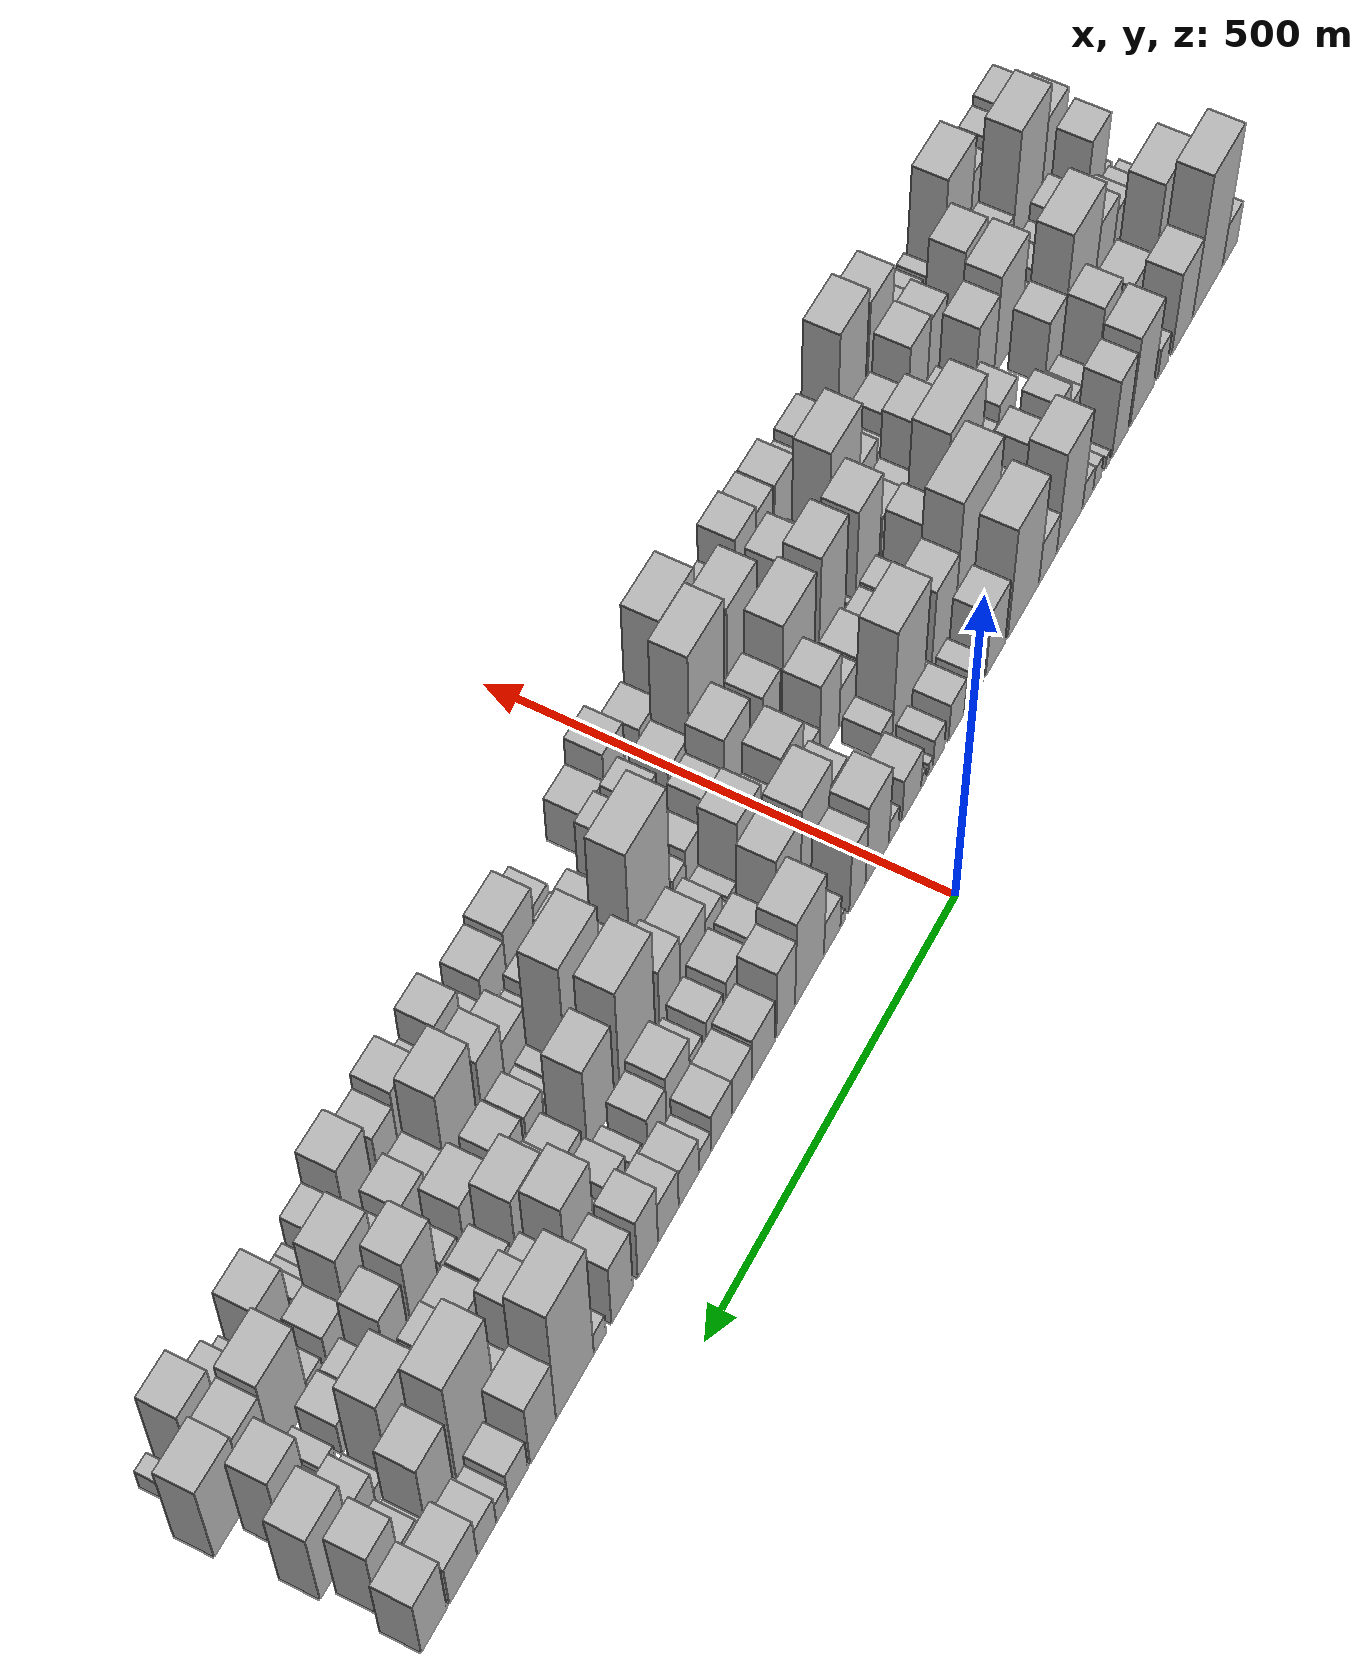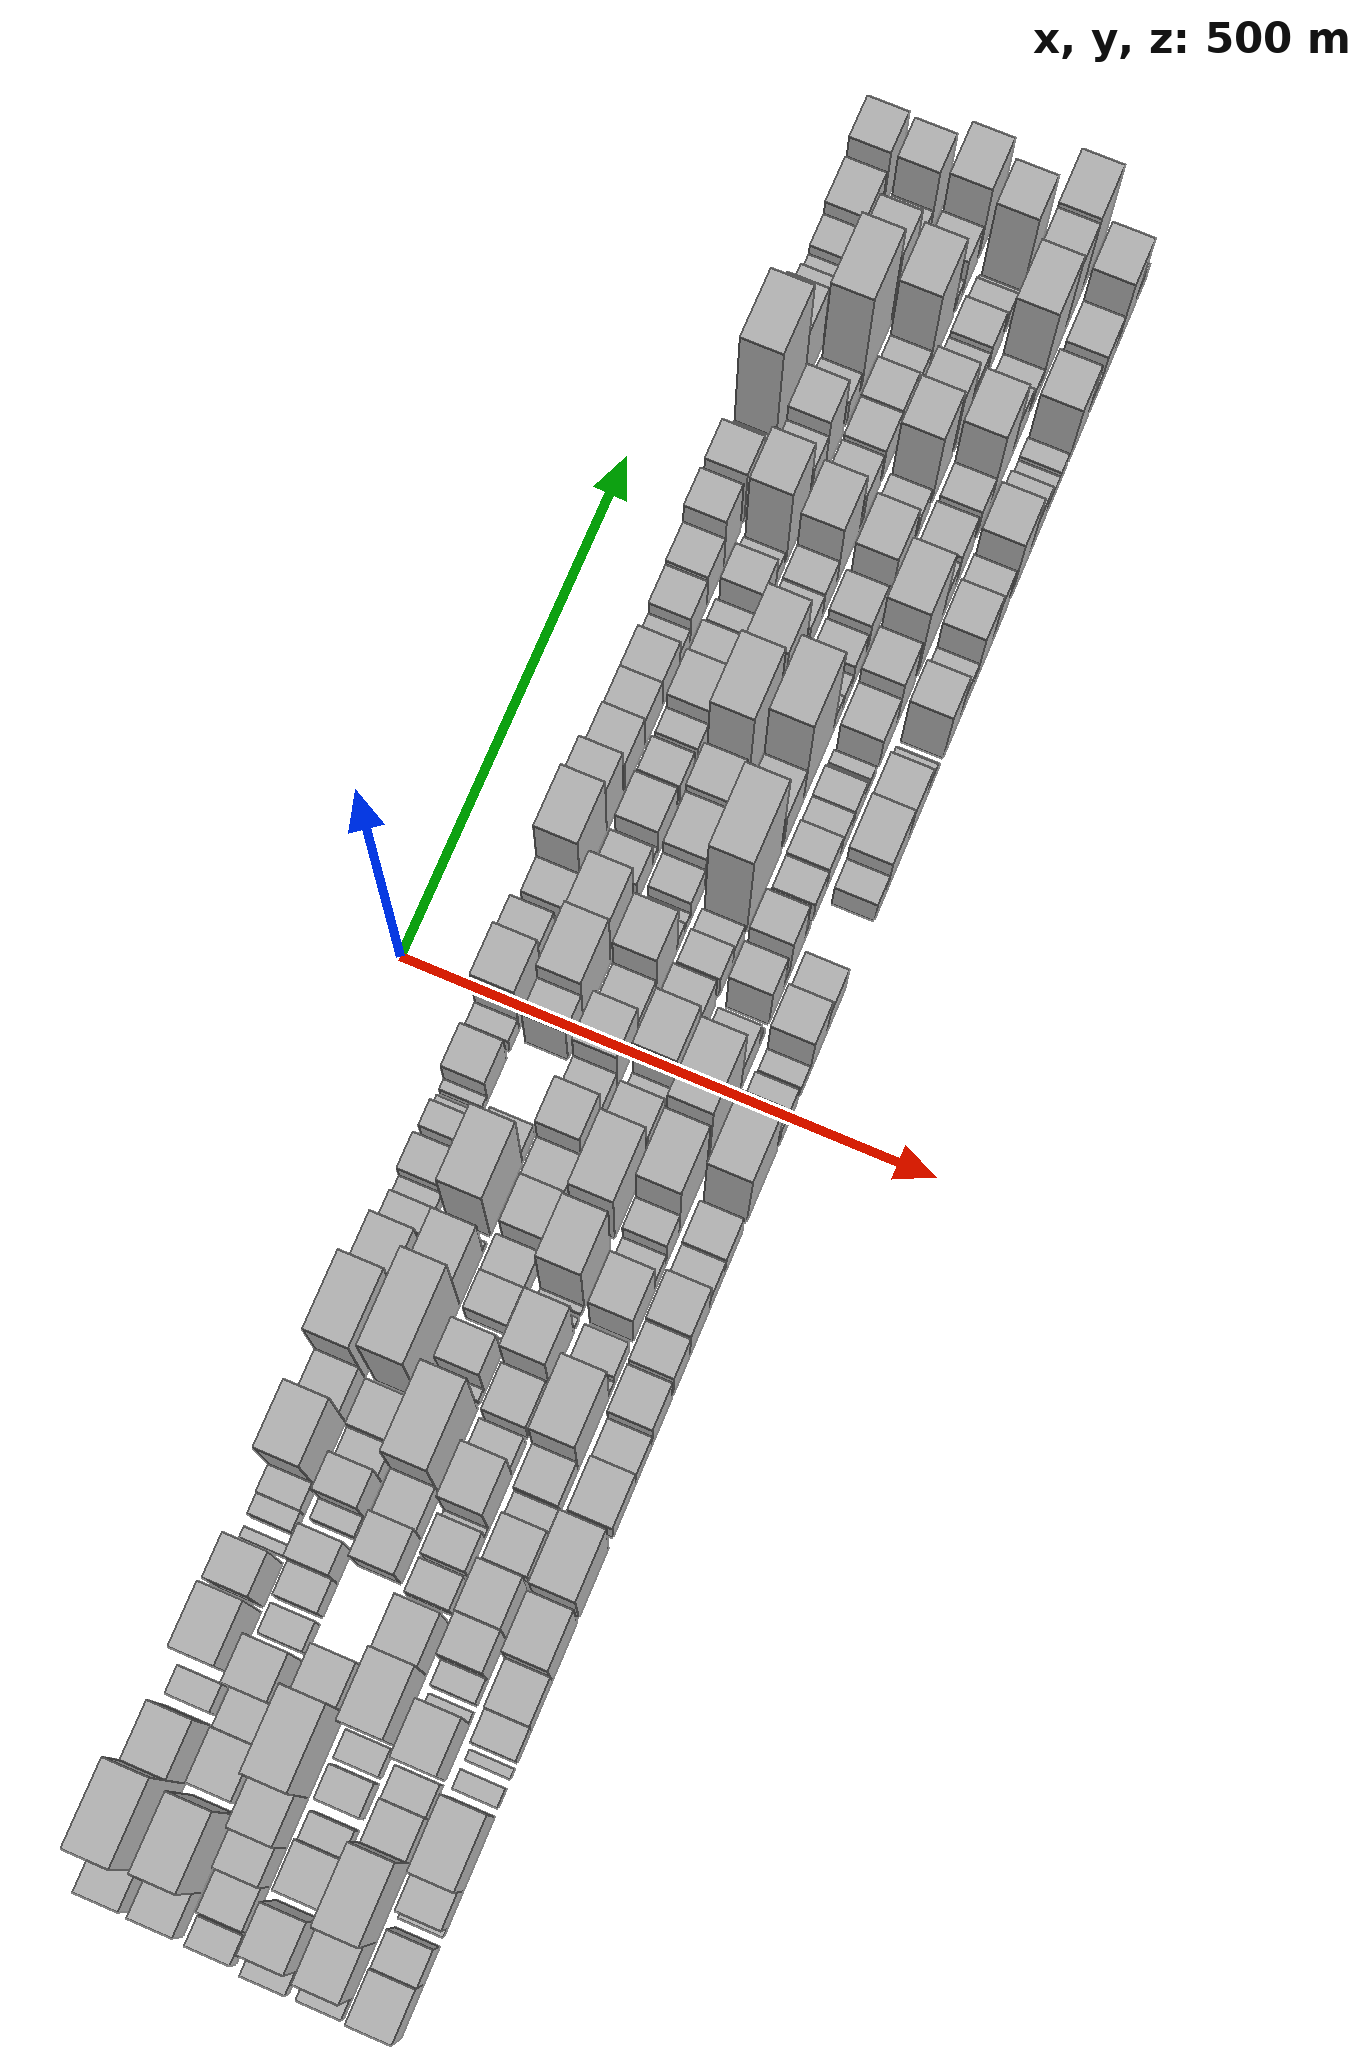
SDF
<sdf version="1.6">
 <world name="default">
  <scene>
   <sky><clouds><speed>12</speed></clouds></sky>
   <ambient>0.4 0.4 0.4 1</ambient>
   <background>0.7 0.7 0.7 1</background>
   <shadows>1</shadows>
  </scene>
  <gravity>0 0 -9.8066</gravity>
  <magnetic_field>6e-06 2.3e-05 -4.2e-05</magnetic_field>
  <physics default="0" name="default_physics" type="ode">
   <ode>
    <solver>
     <type>quick</type>
     <iters>10</iters>
     <sor>1.0</sor>
     <use_dynamic_moi_rescaling>0</use_dynamic_moi_rescaling>
    </solver>
    <constraints>
     <cfm>0</cfm>
     <erp>0.2</erp>
     <contact_max_correcting_vel>100</contact_max_correcting_vel>
     <contact_surface_layer>0.001</contact_surface_layer>
    </constraints>
   </ode>
   <max_step_size>0.004</max_step_size>
   <real_time_factor>1</real_time_factor>
   <real_time_update_rate>250</real_time_update_rate>
  </physics>
  <light name="sun" type="directional">
   <pose>0 0 10 0 0 0</pose>
   <diffuse>0.8 0.8 0.8 1</diffuse>
   <specular>0.2 0.2 0.2 1</specular>
   <attenuation>
    <range>1000</range>
    <constant>0.9</constant>
    <linear>0.01</linear>
    <quadratic>0.001</quadratic>
   </attenuation>
   <direction>-0.5 0.1 -0.9</direction>
  </light>
  <model name="building_1">
   <static>1</static>
   <pose>100.0000 -802.7272 0 0.000000 0.000000 0.000000</pose>
   <link name="link">
    <pose>0 0 33.00 0 0 0</pose>
    <collision name="collision"><geometry><box><size>40.0000 36.5455 66.0000</size></box></geometry></collision>
    <visual name="visual">
     <cast_shadows>0</cast_shadows>
     <geometry><box><size>40.0000 36.5455 66.0000</size></box></geometry>
     <material>
      <script>
       <uri>model://HANNAS_wall/materials/scripts</uri>
       <uri>model://HANNAS_wall/materials/textures</uri>
       <name>vrc/HANNAS_wall</name>
      </script>
     </material>
    </visual>
   </link>
  </model>
  <model name="building_2">
   <static>1</static>
   <pose>100.0000 -747.2606 0 0.000000 0.000000 0.000000</pose>
   <link name="link">
    <pose>0 0 112.50 0 0 0</pose>
    <collision name="collision"><geometry><box><size>40.0000 74.3877 225.0000</size></box></geometry></collision>
    <visual name="visual">
     <cast_shadows>0</cast_shadows>
     <geometry><box><size>40.0000 74.3877 225.0000</size></box></geometry>
     <material>
      <script>
       <uri>model://HANNAS_wall/materials/scripts</uri>
       <uri>model://HANNAS_wall/materials/textures</uri>
       <name>vrc/HANNAS_wall</name>
      </script>
     </material>
    </visual>
   </link>
  </model>
  <model name="building_3">
   <static>1</static>
   <pose>100.0000 -684.5921 0 0.000000 0.000000 0.000000</pose>
   <link name="link">
    <pose>0 0 64.50 0 0 0</pose>
    <collision name="collision"><geometry><box><size>40.0000 50.9493 129.0000</size></box></geometry></collision>
    <visual name="visual">
     <cast_shadows>0</cast_shadows>
     <geometry><box><size>40.0000 50.9493 129.0000</size></box></geometry>
     <material>
      <script>
       <uri>model://HANNAS_wall/materials/scripts</uri>
       <uri>model://HANNAS_wall/materials/textures</uri>
       <name>vrc/HANNAS_wall</name>
      </script>
     </material>
    </visual>
   </link>
  </model>
  <model name="building_4">
   <static>1</static>
   <pose>100.0000 -637.5863 0 0.000000 0.000000 0.000000</pose>
   <link name="link">
    <pose>0 0 24.00 0 0 0</pose>
    <collision name="collision"><geometry><box><size>40.0000 25.0623 48.0000</size></box></geometry></collision>
    <visual name="visual">
     <cast_shadows>0</cast_shadows>
     <geometry><box><size>40.0000 25.0623 48.0000</size></box></geometry>
     <material>
      <script>
       <uri>model://HANNAS_wall/materials/scripts</uri>
       <uri>model://HANNAS_wall/materials/textures</uri>
       <name>vrc/HANNAS_wall</name>
      </script>
     </material>
    </visual>
   </link>
  </model>
  <model name="building_5">
   <static>1</static>
   <pose>100.0000 -586.9120 0 0.000000 0.000000 0.000000</pose>
   <link name="link">
    <pose>0 0 72.00 0 0 0</pose>
    <collision name="collision"><geometry><box><size>40.0000 56.2862 144.0000</size></box></geometry></collision>
    <visual name="visual">
     <cast_shadows>0</cast_shadows>
     <geometry><box><size>40.0000 56.2862 144.0000</size></box></geometry>
     <material>
      <script>
       <uri>model://HANNAS_wall/materials/scripts</uri>
       <uri>model://HANNAS_wall/materials/textures</uri>
       <name>vrc/HANNAS_wall</name>
      </script>
     </material>
    </visual>
   </link>
  </model>
  <model name="building_6">
   <static>1</static>
   <pose>100.0000 -535.0893 0 0.000000 0.000000 0.000000</pose>
   <link name="link">
    <pose>0 0 63.00 0 0 0</pose>
    <collision name="collision"><geometry><box><size>40.0000 39.3591 126.0000</size></box></geometry></collision>
    <visual name="visual">
     <cast_shadows>0</cast_shadows>
     <geometry><box><size>40.0000 39.3591 126.0000</size></box></geometry>
     <material>
      <script>
       <uri>model://HANNAS_wall/materials/scripts</uri>
       <uri>model://HANNAS_wall/materials/textures</uri>
       <name>vrc/HANNAS_wall</name>
      </script>
     </material>
    </visual>
   </link>
  </model>
  <model name="building_7">
   <static>1</static>
   <pose>100.0000 -505.4283 0 0.000000 0.000000 0.000000</pose>
   <link name="link">
    <pose>0 0 10.50 0 0 0</pose>
    <collision name="collision"><geometry><box><size>40.0000 9.9630 21.0000</size></box></geometry></collision>
    <visual name="visual">
     <cast_shadows>0</cast_shadows>
     <geometry><box><size>40.0000 9.9630 21.0000</size></box></geometry>
     <material>
      <script>
       <uri>model://HANNAS_wall/materials/scripts</uri>
       <uri>model://HANNAS_wall/materials/textures</uri>
       <name>vrc/HANNAS_wall</name>
      </script>
     </material>
    </visual>
   </link>
  </model>
  <model name="building_8">
   <static>1</static>
   <pose>100.0000 -481.1696 0 0.000000 0.000000 0.000000</pose>
   <link name="link">
    <pose>0 0 18.00 0 0 0</pose>
    <collision name="collision"><geometry><box><size>40.0000 18.5544 36.0000</size></box></geometry></collision>
    <visual name="visual">
     <cast_shadows>0</cast_shadows>
     <geometry><box><size>40.0000 18.5544 36.0000</size></box></geometry>
     <material>
      <script>
       <uri>model://HANNAS_wall/materials/scripts</uri>
       <uri>model://HANNAS_wall/materials/textures</uri>
       <name>vrc/HANNAS_wall</name>
      </script>
     </material>
    </visual>
   </link>
  </model>
  <model name="building_9">
   <static>1</static>
   <pose>100.0000 -459.4006 0 0.000000 0.000000 0.000000</pose>
   <link name="link">
    <pose>0 0 21.00 0 0 0</pose>
    <collision name="collision"><geometry><box><size>40.0000 24.9837 42.0000</size></box></geometry></collision>
    <visual name="visual">
     <cast_shadows>0</cast_shadows>
     <geometry><box><size>40.0000 24.9837 42.0000</size></box></geometry>
     <material>
      <script>
       <uri>model://HANNAS_wall/materials/scripts</uri>
       <uri>model://HANNAS_wall/materials/textures</uri>
       <name>vrc/HANNAS_wall</name>
      </script>
     </material>
    </visual>
   </link>
  </model>
  <model name="building_10">
   <static>1</static>
   <pose>100.0000 -417.1602 0 0.000000 0.000000 0.000000</pose>
   <link name="link">
    <pose>0 0 82.50 0 0 0</pose>
    <collision name="collision"><geometry><box><size>40.0000 59.4971 165.0000</size></box></geometry></collision>
    <visual name="visual">
     <cast_shadows>0</cast_shadows>
     <geometry><box><size>40.0000 59.4971 165.0000</size></box></geometry>
     <material>
      <script>
       <uri>model://HANNAS_wall/materials/scripts</uri>
       <uri>model://HANNAS_wall/materials/textures</uri>
       <name>vrc/HANNAS_wall</name>
      </script>
     </material>
    </visual>
   </link>
  </model>
  <model name="building_11">
   <static>1</static>
   <pose>100.0000 -367.1721 0 0.000000 0.000000 0.000000</pose>
   <link name="link">
    <pose>0 0 34.50 0 0 0</pose>
    <collision name="collision"><geometry><box><size>40.0000 40.4791 69.0000</size></box></geometry></collision>
    <visual name="visual">
     <cast_shadows>0</cast_shadows>
     <geometry><box><size>40.0000 40.4791 69.0000</size></box></geometry>
     <material>
      <script>
       <uri>model://HANNAS_wall/materials/scripts</uri>
       <uri>model://HANNAS_wall/materials/textures</uri>
       <name>vrc/HANNAS_wall</name>
      </script>
     </material>
    </visual>
   </link>
  </model>
  <model name="building_12">
   <static>1</static>
   <pose>100.0000 -311.9946 0 0.000000 0.000000 0.000000</pose>
   <link name="link">
    <pose>0 0 91.50 0 0 0</pose>
    <collision name="collision"><geometry><box><size>40.0000 69.8759 183.0000</size></box></geometry></collision>
    <visual name="visual">
     <cast_shadows>0</cast_shadows>
     <geometry><box><size>40.0000 69.8759 183.0000</size></box></geometry>
     <material>
      <script>
       <uri>model://HANNAS_wall/materials/scripts</uri>
       <uri>model://HANNAS_wall/materials/textures</uri>
       <name>vrc/HANNAS_wall</name>
      </script>
     </material>
    </visual>
   </link>
  </model>
  <model name="building_13">
   <static>1</static>
   <pose>100.0000 -249.6901 0 0.000000 0.000000 0.000000</pose>
   <link name="link">
    <pose>0 0 54.00 0 0 0</pose>
    <collision name="collision"><geometry><box><size>40.0000 42.7331 108.0000</size></box></geometry></collision>
    <visual name="visual">
     <cast_shadows>0</cast_shadows>
     <geometry><box><size>40.0000 42.7331 108.0000</size></box></geometry>
     <material>
      <script>
       <uri>model://HANNAS_wall/materials/scripts</uri>
       <uri>model://HANNAS_wall/materials/textures</uri>
       <name>vrc/HANNAS_wall</name>
      </script>
     </material>
    </visual>
   </link>
  </model>
  <model name="building_14">
   <static>1</static>
   <pose>100.0000 -210.0288 0 0.000000 0.000000 0.000000</pose>
   <link name="link">
    <pose>0 0 24.00 0 0 0</pose>
    <collision name="collision"><geometry><box><size>40.0000 24.5895 48.0000</size></box></geometry></collision>
    <visual name="visual">
     <cast_shadows>0</cast_shadows>
     <geometry><box><size>40.0000 24.5895 48.0000</size></box></geometry>
     <material>
      <script>
       <uri>model://HANNAS_wall/materials/scripts</uri>
       <uri>model://HANNAS_wall/materials/textures</uri>
       <name>vrc/HANNAS_wall</name>
      </script>
     </material>
    </visual>
   </link>
  </model>
  <model name="building_15">
   <static>1</static>
   <pose>100.0000 -189.3858 0 0.000000 0.000000 0.000000</pose>
   <link name="link">
    <pose>0 0 15.00 0 0 0</pose>
    <collision name="collision"><geometry><box><size>40.0000 16.6964 30.0000</size></box></geometry></collision>
    <visual name="visual">
     <cast_shadows>0</cast_shadows>
     <geometry><box><size>40.0000 16.6964 30.0000</size></box></geometry>
     <material>
      <script>
       <uri>model://HANNAS_wall/materials/scripts</uri>
       <uri>model://HANNAS_wall/materials/textures</uri>
       <name>vrc/HANNAS_wall</name>
      </script>
     </material>
    </visual>
   </link>
  </model>
  <model name="building_16">
   <static>1</static>
   <pose>100.0000 -163.9849 0 0.000000 0.000000 0.000000</pose>
   <link name="link">
    <pose>0 0 31.50 0 0 0</pose>
    <collision name="collision"><geometry><box><size>40.0000 34.1054 63.0000</size></box></geometry></collision>
    <visual name="visual">
     <cast_shadows>0</cast_shadows>
     <geometry><box><size>40.0000 34.1054 63.0000</size></box></geometry>
     <material>
      <script>
       <uri>model://HANNAS_wall/materials/scripts</uri>
       <uri>model://HANNAS_wall/materials/textures</uri>
       <name>vrc/HANNAS_wall</name>
      </script>
     </material>
    </visual>
   </link>
  </model>
  <model name="building_17">
   <static>1</static>
   <pose>100.0000 -125.6724 0 0.000000 0.000000 0.000000</pose>
   <link name="link">
    <pose>0 0 24.00 0 0 0</pose>
    <collision name="collision"><geometry><box><size>40.0000 24.5197 48.0000</size></box></geometry></collision>
    <visual name="visual">
     <cast_shadows>0</cast_shadows>
     <geometry><box><size>40.0000 24.5197 48.0000</size></box></geometry>
     <material>
      <script>
       <uri>model://HANNAS_wall/materials/scripts</uri>
       <uri>model://HANNAS_wall/materials/textures</uri>
       <name>vrc/HANNAS_wall</name>
      </script>
     </material>
    </visual>
   </link>
  </model>
  <model name="building_18">
   <static>1</static>
   <pose>100.0000 -108.2960 0 0.000000 0.000000 0.000000</pose>
   <link name="link">
    <pose>0 0 10.50 0 0 0</pose>
    <collision name="collision"><geometry><box><size>40.0000 10.2332 21.0000</size></box></geometry></collision>
    <visual name="visual">
     <cast_shadows>0</cast_shadows>
     <geometry><box><size>40.0000 10.2332 21.0000</size></box></geometry>
     <material>
      <script>
       <uri>model://HANNAS_wall/materials/scripts</uri>
       <uri>model://HANNAS_wall/materials/textures</uri>
       <name>vrc/HANNAS_wall</name>
      </script>
     </material>
    </visual>
   </link>
  </model>
  <model name="building_19">
   <static>1</static>
   <pose>100.0000 -93.1652 0 0.000000 0.000000 0.000000</pose>
   <link name="link">
    <pose>0 0 10.50 0 0 0</pose>
    <collision name="collision"><geometry><box><size>40.0000 10.0284 21.0000</size></box></geometry></collision>
    <visual name="visual">
     <cast_shadows>0</cast_shadows>
     <geometry><box><size>40.0000 10.0284 21.0000</size></box></geometry>
     <material>
      <script>
       <uri>model://HANNAS_wall/materials/scripts</uri>
       <uri>model://HANNAS_wall/materials/textures</uri>
       <name>vrc/HANNAS_wall</name>
      </script>
     </material>
    </visual>
   </link>
  </model>
  <model name="building_20">
   <static>1</static>
   <pose>100.0000 -67.8375 0 0.000000 0.000000 0.000000</pose>
   <link name="link">
    <pose>0 0 36.00 0 0 0</pose>
    <collision name="collision"><geometry><box><size>40.0000 40.6270 72.0000</size></box></geometry></collision>
    <visual name="visual">
     <cast_shadows>0</cast_shadows>
     <geometry><box><size>40.0000 40.6270 72.0000</size></box></geometry>
     <material>
      <script>
       <uri>model://HANNAS_wall/materials/scripts</uri>
       <uri>model://HANNAS_wall/materials/textures</uri>
       <name>vrc/HANNAS_wall</name>
      </script>
     </material>
    </visual>
   </link>
  </model>
  <model name="building_21">
   <static>1</static>
   <pose>100.0000 -30.2144 0 0.000000 0.000000 0.000000</pose>
   <link name="link">
    <pose>0 0 19.50 0 0 0</pose>
    <collision name="collision"><geometry><box><size>40.0000 20.6191 39.0000</size></box></geometry></collision>
    <visual name="visual">
     <cast_shadows>0</cast_shadows>
     <geometry><box><size>40.0000 20.6191 39.0000</size></box></geometry>
     <material>
      <script>
       <uri>model://HANNAS_wall/materials/scripts</uri>
       <uri>model://HANNAS_wall/materials/textures</uri>
       <name>vrc/HANNAS_wall</name>
      </script>
     </material>
    </visual>
   </link>
  </model>
  <model name="building_22">
   <static>1</static>
   <pose>100.0000 4.3915 0 0.000000 0.000000 0.000000</pose>
   <link name="link">
    <pose>0 0 69.00 0 0 0</pose>
    <collision name="collision"><geometry><box><size>40.0000 48.5927 138.0000</size></box></geometry></collision>
    <visual name="visual">
     <cast_shadows>0</cast_shadows>
     <geometry><box><size>40.0000 48.5927 138.0000</size></box></geometry>
     <material>
      <script>
       <uri>model://HANNAS_wall/materials/scripts</uri>
       <uri>model://HANNAS_wall/materials/textures</uri>
       <name>vrc/HANNAS_wall</name>
      </script>
     </material>
    </visual>
   </link>
  </model>
  <model name="building_23">
   <static>1</static>
   <pose>100.0000 45.3945 0 0.000000 0.000000 0.000000</pose>
   <link name="link">
    <pose>0 0 55.50 0 0 0</pose>
    <collision name="collision"><geometry><box><size>40.0000 33.4134 111.0000</size></box></geometry></collision>
    <visual name="visual">
     <cast_shadows>0</cast_shadows>
     <geometry><box><size>40.0000 33.4134 111.0000</size></box></geometry>
     <material>
      <script>
       <uri>model://HANNAS_wall/materials/scripts</uri>
       <uri>model://HANNAS_wall/materials/textures</uri>
       <name>vrc/HANNAS_wall</name>
      </script>
     </material>
    </visual>
   </link>
  </model>
  <model name="building_24">
   <static>1</static>
   <pose>100.0000 75.6830 0 0.000000 0.000000 0.000000</pose>
   <link name="link">
    <pose>0 0 10.50 0 0 0</pose>
    <collision name="collision"><geometry><box><size>40.0000 9.1636 21.0000</size></box></geometry></collision>
    <visual name="visual">
     <cast_shadows>0</cast_shadows>
     <geometry><box><size>40.0000 9.1636 21.0000</size></box></geometry>
     <material>
      <script>
       <uri>model://HANNAS_wall/materials/scripts</uri>
       <uri>model://HANNAS_wall/materials/textures</uri>
       <name>vrc/HANNAS_wall</name>
      </script>
     </material>
    </visual>
   </link>
  </model>
  <model name="building_25">
   <static>1</static>
   <pose>100.0000 97.0771 0 0.000000 0.000000 0.000000</pose>
   <link name="link">
    <pose>0 0 30.00 0 0 0</pose>
    <collision name="collision"><geometry><box><size>40.0000 33.6245 60.0000</size></box></geometry></collision>
    <visual name="visual">
     <cast_shadows>0</cast_shadows>
     <geometry><box><size>40.0000 33.6245 60.0000</size></box></geometry>
     <material>
      <script>
       <uri>model://HANNAS_wall/materials/scripts</uri>
       <uri>model://HANNAS_wall/materials/textures</uri>
       <name>vrc/HANNAS_wall</name>
      </script>
     </material>
    </visual>
   </link>
  </model>
  <model name="building_26">
   <static>1</static>
   <pose>100.0000 142.9724 0 0.000000 0.000000 0.000000</pose>
   <link name="link">
    <pose>0 0 76.50 0 0 0</pose>
    <collision name="collision"><geometry><box><size>40.0000 58.1661 153.0000</size></box></geometry></collision>
    <visual name="visual">
     <cast_shadows>0</cast_shadows>
     <geometry><box><size>40.0000 58.1661 153.0000</size></box></geometry>
     <material>
      <script>
       <uri>model://HANNAS_wall/materials/scripts</uri>
       <uri>model://HANNAS_wall/materials/textures</uri>
       <name>vrc/HANNAS_wall</name>
      </script>
     </material>
    </visual>
   </link>
  </model>
  <model name="building_27">
   <static>1</static>
   <pose>100.0000 190.6876 0 0.000000 0.000000 0.000000</pose>
   <link name="link">
    <pose>0 0 61.50 0 0 0</pose>
    <collision name="collision"><geometry><box><size>40.0000 37.2642 123.0000</size></box></geometry></collision>
    <visual name="visual">
     <cast_shadows>0</cast_shadows>
     <geometry><box><size>40.0000 37.2642 123.0000</size></box></geometry>
     <material>
      <script>
       <uri>model://HANNAS_wall/materials/scripts</uri>
       <uri>model://HANNAS_wall/materials/textures</uri>
       <name>vrc/HANNAS_wall</name>
      </script>
     </material>
    </visual>
   </link>
  </model>
  <model name="building_28">
   <static>1</static>
   <pose>100.0000 235.1415 0 0.000000 0.000000 0.000000</pose>
   <link name="link">
    <pose>0 0 39.00 0 0 0</pose>
    <collision name="collision"><geometry><box><size>40.0000 45.6437 78.0000</size></box></geometry></collision>
    <visual name="visual">
     <cast_shadows>0</cast_shadows>
     <geometry><box><size>40.0000 45.6437 78.0000</size></box></geometry>
     <material>
      <script>
       <uri>model://HANNAS_wall/materials/scripts</uri>
       <uri>model://HANNAS_wall/materials/textures</uri>
       <name>vrc/HANNAS_wall</name>
      </script>
     </material>
    </visual>
   </link>
  </model>
  <model name="building_29">
   <static>1</static>
   <pose>100.0000 277.3512 0 0.000000 0.000000 0.000000</pose>
   <link name="link">
    <pose>0 0 34.50 0 0 0</pose>
    <collision name="collision"><geometry><box><size>40.0000 38.7757 69.0000</size></box></geometry></collision>
    <visual name="visual">
     <cast_shadows>0</cast_shadows>
     <geometry><box><size>40.0000 38.7757 69.0000</size></box></geometry>
     <material>
      <script>
       <uri>model://HANNAS_wall/materials/scripts</uri>
       <uri>model://HANNAS_wall/materials/textures</uri>
       <name>vrc/HANNAS_wall</name>
      </script>
     </material>
    </visual>
   </link>
  </model>
  <model name="building_30">
   <static>1</static>
   <pose>100.0000 316.5847 0 0.000000 0.000000 0.000000</pose>
   <link name="link">
    <pose>0 0 34.50 0 0 0</pose>
    <collision name="collision"><geometry><box><size>40.0000 39.6913 69.0000</size></box></geometry></collision>
    <visual name="visual">
     <cast_shadows>0</cast_shadows>
     <geometry><box><size>40.0000 39.6913 69.0000</size></box></geometry>
     <material>
      <script>
       <uri>model://HANNAS_wall/materials/scripts</uri>
       <uri>model://HANNAS_wall/materials/textures</uri>
       <name>vrc/HANNAS_wall</name>
      </script>
     </material>
    </visual>
   </link>
  </model>
  <model name="building_31">
   <static>1</static>
   <pose>100.0000 347.9838 0 0.000000 0.000000 0.000000</pose>
   <link name="link">
    <pose>0 0 19.50 0 0 0</pose>
    <collision name="collision"><geometry><box><size>40.0000 23.1069 39.0000</size></box></geometry></collision>
    <visual name="visual">
     <cast_shadows>0</cast_shadows>
     <geometry><box><size>40.0000 23.1069 39.0000</size></box></geometry>
     <material>
      <script>
       <uri>model://HANNAS_wall/materials/scripts</uri>
       <uri>model://HANNAS_wall/materials/textures</uri>
       <name>vrc/HANNAS_wall</name>
      </script>
     </material>
    </visual>
   </link>
  </model>
  <model name="building_32">
   <static>1</static>
   <pose>100.0000 378.6940 0 0.000000 0.000000 0.000000</pose>
   <link name="link">
    <pose>0 0 33.00 0 0 0</pose>
    <collision name="collision"><geometry><box><size>40.0000 38.3136 66.0000</size></box></geometry></collision>
    <visual name="visual">
     <cast_shadows>0</cast_shadows>
     <geometry><box><size>40.0000 38.3136 66.0000</size></box></geometry>
     <material>
      <script>
       <uri>model://HANNAS_wall/materials/scripts</uri>
       <uri>model://HANNAS_wall/materials/textures</uri>
       <name>vrc/HANNAS_wall</name>
      </script>
     </material>
    </visual>
   </link>
  </model>
  <model name="building_33">
   <static>1</static>
   <pose>100.0000 417.2461 0 0.000000 0.000000 0.000000</pose>
   <link name="link">
    <pose>0 0 37.50 0 0 0</pose>
    <collision name="collision"><geometry><box><size>40.0000 38.7907 75.0000</size></box></geometry></collision>
    <visual name="visual">
     <cast_shadows>0</cast_shadows>
     <geometry><box><size>40.0000 38.7907 75.0000</size></box></geometry>
     <material>
      <script>
       <uri>model://HANNAS_wall/materials/scripts</uri>
       <uri>model://HANNAS_wall/materials/textures</uri>
       <name>vrc/HANNAS_wall</name>
      </script>
     </material>
    </visual>
   </link>
  </model>
  <model name="building_34">
   <static>1</static>
   <pose>100.0000 455.6009 0 0.000000 0.000000 0.000000</pose>
   <link name="link">
    <pose>0 0 57.00 0 0 0</pose>
    <collision name="collision"><geometry><box><size>40.0000 37.9189 114.0000</size></box></geometry></collision>
    <visual name="visual">
     <cast_shadows>0</cast_shadows>
     <geometry><box><size>40.0000 37.9189 114.0000</size></box></geometry>
     <material>
      <script>
       <uri>model://HANNAS_wall/materials/scripts</uri>
       <uri>model://HANNAS_wall/materials/textures</uri>
       <name>vrc/HANNAS_wall</name>
      </script>
     </material>
    </visual>
   </link>
  </model>
  <model name="building_35">
   <static>1</static>
   <pose>100.0000 503.2445 0 0.000000 0.000000 0.000000</pose>
   <link name="link">
    <pose>0 0 57.00 0 0 0</pose>
    <collision name="collision"><geometry><box><size>40.0000 39.3681 114.0000</size></box></geometry></collision>
    <visual name="visual">
     <cast_shadows>0</cast_shadows>
     <geometry><box><size>40.0000 39.3681 114.0000</size></box></geometry>
     <material>
      <script>
       <uri>model://HANNAS_wall/materials/scripts</uri>
       <uri>model://HANNAS_wall/materials/textures</uri>
       <name>vrc/HANNAS_wall</name>
      </script>
     </material>
    </visual>
   </link>
  </model>
  <model name="building_36">
   <static>1</static>
   <pose>100.0000 543.7917 0 0.000000 0.000000 0.000000</pose>
   <link name="link">
    <pose>0 0 19.50 0 0 0</pose>
    <collision name="collision"><geometry><box><size>40.0000 21.7262 39.0000</size></box></geometry></collision>
    <visual name="visual">
     <cast_shadows>0</cast_shadows>
     <geometry><box><size>40.0000 21.7262 39.0000</size></box></geometry>
     <material>
      <script>
       <uri>model://HANNAS_wall/materials/scripts</uri>
       <uri>model://HANNAS_wall/materials/textures</uri>
       <name>vrc/HANNAS_wall</name>
      </script>
     </material>
    </visual>
   </link>
  </model>
  <model name="building_37">
   <static>1</static>
   <pose>100.0000 588.7584 0 0.000000 0.000000 0.000000</pose>
   <link name="link">
    <pose>0 0 109.50 0 0 0</pose>
    <collision name="collision"><geometry><box><size>40.0000 68.2071 219.0000</size></box></geometry></collision>
    <visual name="visual">
     <cast_shadows>0</cast_shadows>
     <geometry><box><size>40.0000 68.2071 219.0000</size></box></geometry>
     <material>
      <script>
       <uri>model://HANNAS_wall/materials/scripts</uri>
       <uri>model://HANNAS_wall/materials/textures</uri>
       <name>vrc/HANNAS_wall</name>
      </script>
     </material>
    </visual>
   </link>
  </model>
  <model name="building_38">
   <static>1</static>
   <pose>100.0000 645.7755 0 0.000000 0.000000 0.000000</pose>
   <link name="link">
    <pose>0 0 60.00 0 0 0</pose>
    <collision name="collision"><geometry><box><size>40.0000 45.8273 120.0000</size></box></geometry></collision>
    <visual name="visual">
     <cast_shadows>0</cast_shadows>
     <geometry><box><size>40.0000 45.8273 120.0000</size></box></geometry>
     <material>
      <script>
       <uri>model://HANNAS_wall/materials/scripts</uri>
       <uri>model://HANNAS_wall/materials/textures</uri>
       <name>vrc/HANNAS_wall</name>
      </script>
     </material>
    </visual>
   </link>
  </model>
  <model name="building_39">
   <static>1</static>
   <pose>100.0000 689.8331 0 0.000000 0.000000 0.000000</pose>
   <link name="link">
    <pose>0 0 30.00 0 0 0</pose>
    <collision name="collision"><geometry><box><size>40.0000 34.2878 60.0000</size></box></geometry></collision>
    <visual name="visual">
     <cast_shadows>0</cast_shadows>
     <geometry><box><size>40.0000 34.2878 60.0000</size></box></geometry>
     <material>
      <script>
       <uri>model://HANNAS_wall/materials/scripts</uri>
       <uri>model://HANNAS_wall/materials/textures</uri>
       <name>vrc/HANNAS_wall</name>
      </script>
     </material>
    </visual>
   </link>
  </model>
  <model name="building_40">
   <static>1</static>
   <pose>100.0000 717.3259 0 0.000000 0.000000 0.000000</pose>
   <link name="link">
    <pose>0 0 19.50 0 0 0</pose>
    <collision name="collision"><geometry><box><size>40.0000 20.6979 39.0000</size></box></geometry></collision>
    <visual name="visual">
     <cast_shadows>0</cast_shadows>
     <geometry><box><size>40.0000 20.6979 39.0000</size></box></geometry>
     <material>
      <script>
       <uri>model://HANNAS_wall/materials/scripts</uri>
       <uri>model://HANNAS_wall/materials/textures</uri>
       <name>vrc/HANNAS_wall</name>
      </script>
     </material>
    </visual>
   </link>
  </model>
  <model name="building_41">
   <static>1</static>
   <pose>100.0000 744.1089 0 0.000000 0.000000 0.000000</pose>
   <link name="link">
    <pose>0 0 28.50 0 0 0</pose>
    <collision name="collision"><geometry><box><size>40.0000 32.8681 57.0000</size></box></geometry></collision>
    <visual name="visual">
     <cast_shadows>0</cast_shadows>
     <geometry><box><size>40.0000 32.8681 57.0000</size></box></geometry>
     <material>
      <script>
       <uri>model://HANNAS_wall/materials/scripts</uri>
       <uri>model://HANNAS_wall/materials/textures</uri>
       <name>vrc/HANNAS_wall</name>
      </script>
     </material>
    </visual>
   </link>
  </model>
  <model name="building_42">
   <static>1</static>
   <pose>100.0000 784.3606 0 0.000000 0.000000 0.000000</pose>
   <link name="link">
    <pose>0 0 40.50 0 0 0</pose>
    <collision name="collision"><geometry><box><size>40.0000 47.6351 81.0000</size></box></geometry></collision>
    <visual name="visual">
     <cast_shadows>0</cast_shadows>
     <geometry><box><size>40.0000 47.6351 81.0000</size></box></geometry>
     <material>
      <script>
       <uri>model://HANNAS_wall/materials/scripts</uri>
       <uri>model://HANNAS_wall/materials/textures</uri>
       <name>vrc/HANNAS_wall</name>
      </script>
     </material>
    </visual>
   </link>
  </model>
  <model name="building_43">
   <static>1</static>
   <pose>100.0000 833.8512 0 0.000000 0.000000 0.000000</pose>
   <link name="link">
    <pose>0 0 55.50 0 0 0</pose>
    <collision name="collision"><geometry><box><size>40.0000 43.3461 111.0000</size></box></geometry></collision>
    <visual name="visual">
     <cast_shadows>0</cast_shadows>
     <geometry><box><size>40.0000 43.3461 111.0000</size></box></geometry>
     <material>
      <script>
       <uri>model://HANNAS_wall/materials/scripts</uri>
       <uri>model://HANNAS_wall/materials/textures</uri>
       <name>vrc/HANNAS_wall</name>
      </script>
     </material>
    </visual>
   </link>
  </model>
  <model name="building_44">
   <static>1</static>
   <pose>149.0000 -803.0353 0 0.000000 0.000000 0.000000</pose>
   <link name="link">
    <pose>0 0 36.00 0 0 0</pose>
    <collision name="collision"><geometry><box><size>40.0000 37.9294 72.0000</size></box></geometry></collision>
    <visual name="visual">
     <cast_shadows>0</cast_shadows>
     <geometry><box><size>40.0000 37.9294 72.0000</size></box></geometry>
     <material>
      <script>
       <uri>model://HANNAS_wall/materials/scripts</uri>
       <uri>model://HANNAS_wall/materials/textures</uri>
       <name>vrc/HANNAS_wall</name>
      </script>
     </material>
    </visual>
   </link>
  </model>
  <model name="building_45">
   <static>1</static>
   <pose>149.0000 -750.1033 0 0.000000 0.000000 0.000000</pose>
   <link name="link">
    <pose>0 0 88.50 0 0 0</pose>
    <collision name="collision"><geometry><box><size>40.0000 67.9345 177.0000</size></box></geometry></collision>
    <visual name="visual">
     <cast_shadows>0</cast_shadows>
     <geometry><box><size>40.0000 67.9345 177.0000</size></box></geometry>
     <material>
      <script>
       <uri>model://HANNAS_wall/materials/scripts</uri>
       <uri>model://HANNAS_wall/materials/textures</uri>
       <name>vrc/HANNAS_wall</name>
      </script>
     </material>
    </visual>
   </link>
  </model>
  <model name="building_46">
   <static>1</static>
   <pose>149.0000 -683.1631 0 0.000000 0.000000 0.000000</pose>
   <link name="link">
    <pose>0 0 40.50 0 0 0</pose>
    <collision name="collision"><geometry><box><size>40.0000 47.9459 81.0000</size></box></geometry></collision>
    <visual name="visual">
     <cast_shadows>0</cast_shadows>
     <geometry><box><size>40.0000 47.9459 81.0000</size></box></geometry>
     <material>
      <script>
       <uri>model://HANNAS_wall/materials/scripts</uri>
       <uri>model://HANNAS_wall/materials/textures</uri>
       <name>vrc/HANNAS_wall</name>
      </script>
     </material>
    </visual>
   </link>
  </model>
  <model name="building_47">
   <static>1</static>
   <pose>149.0000 -641.7126 0 0.000000 0.000000 0.000000</pose>
   <link name="link">
    <pose>0 0 34.50 0 0 0</pose>
    <collision name="collision"><geometry><box><size>40.0000 34.9551 69.0000</size></box></geometry></collision>
    <visual name="visual">
     <cast_shadows>0</cast_shadows>
     <geometry><box><size>40.0000 34.9551 69.0000</size></box></geometry>
     <material>
      <script>
       <uri>model://HANNAS_wall/materials/scripts</uri>
       <uri>model://HANNAS_wall/materials/textures</uri>
       <name>vrc/HANNAS_wall</name>
      </script>
     </material>
    </visual>
   </link>
  </model>
  <model name="building_48">
   <static>1</static>
   <pose>149.0000 -603.1813 0 0.000000 0.000000 0.000000</pose>
   <link name="link">
    <pose>0 0 67.50 0 0 0</pose>
    <collision name="collision"><geometry><box><size>40.0000 42.1076 135.0000</size></box></geometry></collision>
    <visual name="visual">
     <cast_shadows>0</cast_shadows>
     <geometry><box><size>40.0000 42.1076 135.0000</size></box></geometry>
     <material>
      <script>
       <uri>model://HANNAS_wall/materials/scripts</uri>
       <uri>model://HANNAS_wall/materials/textures</uri>
       <name>vrc/HANNAS_wall</name>
      </script>
     </material>
    </visual>
   </link>
  </model>
  <model name="building_49">
   <static>1</static>
   <pose>149.0000 -562.7441 0 0.000000 0.000000 0.000000</pose>
   <link name="link">
    <pose>0 0 22.50 0 0 0</pose>
    <collision name="collision"><geometry><box><size>40.0000 26.7669 45.0000</size></box></geometry></collision>
    <visual name="visual">
     <cast_shadows>0</cast_shadows>
     <geometry><box><size>40.0000 26.7669 45.0000</size></box></geometry>
     <material>
      <script>
       <uri>model://HANNAS_wall/materials/scripts</uri>
       <uri>model://HANNAS_wall/materials/textures</uri>
       <name>vrc/HANNAS_wall</name>
      </script>
     </material>
    </visual>
   </link>
  </model>
  <model name="building_50">
   <static>1</static>
   <pose>149.0000 -528.2144 0 0.000000 0.000000 0.000000</pose>
   <link name="link">
    <pose>0 0 28.50 0 0 0</pose>
    <collision name="collision"><geometry><box><size>40.0000 30.2926 57.0000</size></box></geometry></collision>
    <visual name="visual">
     <cast_shadows>0</cast_shadows>
     <geometry><box><size>40.0000 30.2926 57.0000</size></box></geometry>
     <material>
      <script>
       <uri>model://HANNAS_wall/materials/scripts</uri>
       <uri>model://HANNAS_wall/materials/textures</uri>
       <name>vrc/HANNAS_wall</name>
      </script>
     </material>
    </visual>
   </link>
  </model>
  <model name="building_51">
   <static>1</static>
   <pose>149.0000 -498.4936 0 0.000000 0.000000 0.000000</pose>
   <link name="link">
    <pose>0 0 48.00 0 0 0</pose>
    <collision name="collision"><geometry><box><size>40.0000 29.1489 96.0000</size></box></geometry></collision>
    <visual name="visual">
     <cast_shadows>0</cast_shadows>
     <geometry><box><size>40.0000 29.1489 96.0000</size></box></geometry>
     <material>
      <script>
       <uri>model://HANNAS_wall/materials/scripts</uri>
       <uri>model://HANNAS_wall/materials/textures</uri>
       <name>vrc/HANNAS_wall</name>
      </script>
     </material>
    </visual>
   </link>
  </model>
  <model name="building_52">
   <static>1</static>
   <pose>149.0000 -464.7220 0 0.000000 0.000000 0.000000</pose>
   <link name="link">
    <pose>0 0 16.50 0 0 0</pose>
    <collision name="collision"><geometry><box><size>40.0000 18.3942 33.0000</size></box></geometry></collision>
    <visual name="visual">
     <cast_shadows>0</cast_shadows>
     <geometry><box><size>40.0000 18.3942 33.0000</size></box></geometry>
     <material>
      <script>
       <uri>model://HANNAS_wall/materials/scripts</uri>
       <uri>model://HANNAS_wall/materials/textures</uri>
       <name>vrc/HANNAS_wall</name>
      </script>
     </material>
    </visual>
   </link>
  </model>
  <model name="building_53">
   <static>1</static>
   <pose>149.0000 -438.6928 0 0.000000 0.000000 0.000000</pose>
   <link name="link">
    <pose>0 0 52.50 0 0 0</pose>
    <collision name="collision"><geometry><box><size>40.0000 33.6643 105.0000</size></box></geometry></collision>
    <visual name="visual">
     <cast_shadows>0</cast_shadows>
     <geometry><box><size>40.0000 33.6643 105.0000</size></box></geometry>
     <material>
      <script>
       <uri>model://HANNAS_wall/materials/scripts</uri>
       <uri>model://HANNAS_wall/materials/textures</uri>
       <name>vrc/HANNAS_wall</name>
      </script>
     </material>
    </visual>
   </link>
  </model>
  <model name="building_54">
   <static>1</static>
   <pose>149.0000 -407.9433 0 0.000000 0.000000 0.000000</pose>
   <link name="link">
    <pose>0 0 27.00 0 0 0</pose>
    <collision name="collision"><geometry><box><size>40.0000 27.8346 54.0000</size></box></geometry></collision>
    <visual name="visual">
     <cast_shadows>0</cast_shadows>
     <geometry><box><size>40.0000 27.8346 54.0000</size></box></geometry>
     <material>
      <script>
       <uri>model://HANNAS_wall/materials/scripts</uri>
       <uri>model://HANNAS_wall/materials/textures</uri>
       <name>vrc/HANNAS_wall</name>
      </script>
     </material>
    </visual>
   </link>
  </model>
  <model name="building_55">
   <static>1</static>
   <pose>149.0000 -373.6690 0 0.000000 0.000000 0.000000</pose>
   <link name="link">
    <pose>0 0 37.50 0 0 0</pose>
    <collision name="collision"><geometry><box><size>40.0000 40.7140 75.0000</size></box></geometry></collision>
    <visual name="visual">
     <cast_shadows>0</cast_shadows>
     <geometry><box><size>40.0000 40.7140 75.0000</size></box></geometry>
     <material>
      <script>
       <uri>model://HANNAS_wall/materials/scripts</uri>
       <uri>model://HANNAS_wall/materials/textures</uri>
       <name>vrc/HANNAS_wall</name>
      </script>
     </material>
    </visual>
   </link>
  </model>
  <model name="building_56">
   <static>1</static>
   <pose>149.0000 -302.2991 0 0.000000 0.000000 0.000000</pose>
   <link name="link">
    <pose>0 0 108.00 0 0 0</pose>
    <collision name="collision"><geometry><box><size>40.0000 86.0258 216.0000</size></box></geometry></collision>
    <visual name="visual">
     <cast_shadows>0</cast_shadows>
     <geometry><box><size>40.0000 86.0258 216.0000</size></box></geometry>
     <material>
      <script>
       <uri>model://HANNAS_wall/materials/scripts</uri>
       <uri>model://HANNAS_wall/materials/textures</uri>
       <name>vrc/HANNAS_wall</name>
      </script>
     </material>
    </visual>
   </link>
  </model>
  <model name="building_57">
   <static>1</static>
   <pose>149.0000 -234.6798 0 0.000000 0.000000 0.000000</pose>
   <link name="link">
    <pose>0 0 67.50 0 0 0</pose>
    <collision name="collision"><geometry><box><size>40.0000 49.2129 135.0000</size></box></geometry></collision>
    <visual name="visual">
     <cast_shadows>0</cast_shadows>
     <geometry><box><size>40.0000 49.2129 135.0000</size></box></geometry>
     <material>
      <script>
       <uri>model://HANNAS_wall/materials/scripts</uri>
       <uri>model://HANNAS_wall/materials/textures</uri>
       <name>vrc/HANNAS_wall</name>
      </script>
     </material>
    </visual>
   </link>
  </model>
  <model name="building_58">
   <static>1</static>
   <pose>149.0000 -206.4433 0 0.000000 0.000000 0.000000</pose>
   <link name="link">
    <pose>0 0 7.50 0 0 0</pose>
    <collision name="collision"><geometry><box><size>40.0000 7.2601 15.0000</size></box></geometry></collision>
    <visual name="visual">
     <cast_shadows>0</cast_shadows>
     <geometry><box><size>40.0000 7.2601 15.0000</size></box></geometry>
     <material>
      <script>
       <uri>model://HANNAS_wall/materials/scripts</uri>
       <uri>model://HANNAS_wall/materials/textures</uri>
       <name>vrc/HANNAS_wall</name>
      </script>
     </material>
    </visual>
   </link>
  </model>
  <model name="building_59">
   <static>1</static>
   <pose>149.0000 -160.5420 0 0.000000 0.000000 0.000000</pose>
   <link name="link">
    <pose>0 0 90.00 0 0 0</pose>
    <collision name="collision"><geometry><box><size>40.0000 68.5425 180.0000</size></box></geometry></collision>
    <visual name="visual">
     <cast_shadows>0</cast_shadows>
     <geometry><box><size>40.0000 68.5425 180.0000</size></box></geometry>
     <material>
      <script>
       <uri>model://HANNAS_wall/materials/scripts</uri>
       <uri>model://HANNAS_wall/materials/textures</uri>
       <name>vrc/HANNAS_wall</name>
      </script>
     </material>
    </visual>
   </link>
  </model>
  <model name="building_60">
   <static>1</static>
   <pose>149.0000 -112.8269 0 0.000000 0.000000 0.000000</pose>
   <link name="link">
    <pose>0 0 22.50 0 0 0</pose>
    <collision name="collision"><geometry><box><size>40.0000 26.8878 45.0000</size></box></geometry></collision>
    <visual name="visual">
     <cast_shadows>0</cast_shadows>
     <geometry><box><size>40.0000 26.8878 45.0000</size></box></geometry>
     <material>
      <script>
       <uri>model://HANNAS_wall/materials/scripts</uri>
       <uri>model://HANNAS_wall/materials/textures</uri>
       <name>vrc/HANNAS_wall</name>
      </script>
     </material>
    </visual>
   </link>
  </model>
  <model name="building_61">
   <static>1</static>
   <pose>149.0000 -10.8779 0 0.000000 0.000000 0.000000</pose>
   <link name="link">
    <pose>0 0 54.00 0 0 0</pose>
    <collision name="collision"><geometry><box><size>40.0000 33.6701 108.0000</size></box></geometry></collision>
    <visual name="visual">
     <cast_shadows>0</cast_shadows>
     <geometry><box><size>40.0000 33.6701 108.0000</size></box></geometry>
     <material>
      <script>
       <uri>model://HANNAS_wall/materials/scripts</uri>
       <uri>model://HANNAS_wall/materials/textures</uri>
       <name>vrc/HANNAS_wall</name>
      </script>
     </material>
    </visual>
   </link>
  </model>
  <model name="building_62">
   <static>1</static>
   <pose>149.0000 35.7177 0 0.000000 0.000000 0.000000</pose>
   <link name="link">
    <pose>0 0 75.00 0 0 0</pose>
    <collision name="collision"><geometry><box><size>40.0000 59.5212 150.0000</size></box></geometry></collision>
    <visual name="visual">
     <cast_shadows>0</cast_shadows>
     <geometry><box><size>40.0000 59.5212 150.0000</size></box></geometry>
     <material>
      <script>
       <uri>model://HANNAS_wall/materials/scripts</uri>
       <uri>model://HANNAS_wall/materials/textures</uri>
       <name>vrc/HANNAS_wall</name>
      </script>
     </material>
    </visual>
   </link>
  </model>
  <model name="building_63">
   <static>1</static>
   <pose>149.0000 90.9288 0 0.000000 0.000000 0.000000</pose>
   <link name="link">
    <pose>0 0 69.00 0 0 0</pose>
    <collision name="collision"><geometry><box><size>40.0000 50.9010 138.0000</size></box></geometry></collision>
    <visual name="visual">
     <cast_shadows>0</cast_shadows>
     <geometry><box><size>40.0000 50.9010 138.0000</size></box></geometry>
     <material>
      <script>
       <uri>model://HANNAS_wall/materials/scripts</uri>
       <uri>model://HANNAS_wall/materials/textures</uri>
       <name>vrc/HANNAS_wall</name>
      </script>
     </material>
    </visual>
   </link>
  </model>
  <model name="building_64">
   <static>1</static>
   <pose>149.0000 141.6008 0 0.000000 0.000000 0.000000</pose>
   <link name="link">
    <pose>0 0 31.50 0 0 0</pose>
    <collision name="collision"><geometry><box><size>40.0000 36.4432 63.0000</size></box></geometry></collision>
    <visual name="visual">
     <cast_shadows>0</cast_shadows>
     <geometry><box><size>40.0000 36.4432 63.0000</size></box></geometry>
     <material>
      <script>
       <uri>model://HANNAS_wall/materials/scripts</uri>
       <uri>model://HANNAS_wall/materials/textures</uri>
       <name>vrc/HANNAS_wall</name>
      </script>
     </material>
    </visual>
   </link>
  </model>
  <model name="building_65">
   <static>1</static>
   <pose>149.0000 165.2321 0 0.000000 0.000000 0.000000</pose>
   <link name="link">
    <pose>0 0 12.00 0 0 0</pose>
    <collision name="collision"><geometry><box><size>40.0000 10.8193 24.0000</size></box></geometry></collision>
    <visual name="visual">
     <cast_shadows>0</cast_shadows>
     <geometry><box><size>40.0000 10.8193 24.0000</size></box></geometry>
     <material>
      <script>
       <uri>model://HANNAS_wall/materials/scripts</uri>
       <uri>model://HANNAS_wall/materials/textures</uri>
       <name>vrc/HANNAS_wall</name>
      </script>
     </material>
    </visual>
   </link>
  </model>
  <model name="building_66">
   <static>1</static>
   <pose>149.0000 192.1808 0 0.000000 0.000000 0.000000</pose>
   <link name="link">
    <pose>0 0 36.00 0 0 0</pose>
    <collision name="collision"><geometry><box><size>40.0000 43.0781 72.0000</size></box></geometry></collision>
    <visual name="visual">
     <cast_shadows>0</cast_shadows>
     <geometry><box><size>40.0000 43.0781 72.0000</size></box></geometry>
     <material>
      <script>
       <uri>model://HANNAS_wall/materials/scripts</uri>
       <uri>model://HANNAS_wall/materials/textures</uri>
       <name>vrc/HANNAS_wall</name>
      </script>
     </material>
    </visual>
   </link>
  </model>
  <model name="building_67">
   <static>1</static>
   <pose>149.0000 235.2447 0 0.000000 0.000000 0.000000</pose>
   <link name="link">
    <pose>0 0 30.00 0 0 0</pose>
    <collision name="collision"><geometry><box><size>40.0000 33.0497 60.0000</size></box></geometry></collision>
    <visual name="visual">
     <cast_shadows>0</cast_shadows>
     <geometry><box><size>40.0000 33.0497 60.0000</size></box></geometry>
     <material>
      <script>
       <uri>model://HANNAS_wall/materials/scripts</uri>
       <uri>model://HANNAS_wall/materials/textures</uri>
       <name>vrc/HANNAS_wall</name>
      </script>
     </material>
    </visual>
   </link>
  </model>
  <model name="building_68">
   <static>1</static>
   <pose>149.0000 255.4464 0 0.000000 0.000000 0.000000</pose>
   <link name="link">
    <pose>0 0 9.00 0 0 0</pose>
    <collision name="collision"><geometry><box><size>40.0000 7.3537 18.0000</size></box></geometry></collision>
    <visual name="visual">
     <cast_shadows>0</cast_shadows>
     <geometry><box><size>40.0000 7.3537 18.0000</size></box></geometry>
     <material>
      <script>
       <uri>model://HANNAS_wall/materials/scripts</uri>
       <uri>model://HANNAS_wall/materials/textures</uri>
       <name>vrc/HANNAS_wall</name>
      </script>
     </material>
    </visual>
   </link>
  </model>
  <model name="building_69">
   <static>1</static>
   <pose>149.0000 271.4099 0 0.000000 0.000000 0.000000</pose>
   <link name="link">
    <pose>0 0 24.00 0 0 0</pose>
    <collision name="collision"><geometry><box><size>40.0000 24.5733 48.0000</size></box></geometry></collision>
    <visual name="visual">
     <cast_shadows>0</cast_shadows>
     <geometry><box><size>40.0000 24.5733 48.0000</size></box></geometry>
     <material>
      <script>
       <uri>model://HANNAS_wall/materials/scripts</uri>
       <uri>model://HANNAS_wall/materials/textures</uri>
       <name>vrc/HANNAS_wall</name>
      </script>
     </material>
    </visual>
   </link>
  </model>
  <model name="building_70">
   <static>1</static>
   <pose>149.0000 306.1748 0 0.000000 0.000000 0.000000</pose>
   <link name="link">
    <pose>0 0 42.00 0 0 0</pose>
    <collision name="collision"><geometry><box><size>40.0000 44.9565 84.0000</size></box></geometry></collision>
    <visual name="visual">
     <cast_shadows>0</cast_shadows>
     <geometry><box><size>40.0000 44.9565 84.0000</size></box></geometry>
     <material>
      <script>
       <uri>model://HANNAS_wall/materials/scripts</uri>
       <uri>model://HANNAS_wall/materials/textures</uri>
       <name>vrc/HANNAS_wall</name>
      </script>
     </material>
    </visual>
   </link>
  </model>
  <model name="building_71">
   <static>1</static>
   <pose>149.0000 346.3911 0 0.000000 0.000000 0.000000</pose>
   <link name="link">
    <pose>0 0 33.00 0 0 0</pose>
    <collision name="collision"><geometry><box><size>40.0000 35.4761 66.0000</size></box></geometry></collision>
    <visual name="visual">
     <cast_shadows>0</cast_shadows>
     <geometry><box><size>40.0000 35.4761 66.0000</size></box></geometry>
     <material>
      <script>
       <uri>model://HANNAS_wall/materials/scripts</uri>
       <uri>model://HANNAS_wall/materials/textures</uri>
       <name>vrc/HANNAS_wall</name>
      </script>
     </material>
    </visual>
   </link>
  </model>
  <model name="building_72">
   <static>1</static>
   <pose>149.0000 384.5979 0 0.000000 0.000000 0.000000</pose>
   <link name="link">
    <pose>0 0 19.50 0 0 0</pose>
    <collision name="collision"><geometry><box><size>40.0000 20.9376 39.0000</size></box></geometry></collision>
    <visual name="visual">
     <cast_shadows>0</cast_shadows>
     <geometry><box><size>40.0000 20.9376 39.0000</size></box></geometry>
     <material>
      <script>
       <uri>model://HANNAS_wall/materials/scripts</uri>
       <uri>model://HANNAS_wall/materials/textures</uri>
       <name>vrc/HANNAS_wall</name>
      </script>
     </material>
    </visual>
   </link>
  </model>
  <model name="building_73">
   <static>1</static>
   <pose>149.0000 421.4805 0 0.000000 0.000000 0.000000</pose>
   <link name="link">
    <pose>0 0 34.50 0 0 0</pose>
    <collision name="collision"><geometry><box><size>40.0000 34.8275 69.0000</size></box></geometry></collision>
    <visual name="visual">
     <cast_shadows>0</cast_shadows>
     <geometry><box><size>40.0000 34.8275 69.0000</size></box></geometry>
     <material>
      <script>
       <uri>model://HANNAS_wall/materials/scripts</uri>
       <uri>model://HANNAS_wall/materials/textures</uri>
       <name>vrc/HANNAS_wall</name>
      </script>
     </material>
    </visual>
   </link>
  </model>
  <model name="building_74">
   <static>1</static>
   <pose>149.0000 448.7668 0 0.000000 0.000000 0.000000</pose>
   <link name="link">
    <pose>0 0 18.00 0 0 0</pose>
    <collision name="collision"><geometry><box><size>40.0000 19.7451 36.0000</size></box></geometry></collision>
    <visual name="visual">
     <cast_shadows>0</cast_shadows>
     <geometry><box><size>40.0000 19.7451 36.0000</size></box></geometry>
     <material>
      <script>
       <uri>model://HANNAS_wall/materials/scripts</uri>
       <uri>model://HANNAS_wall/materials/textures</uri>
       <name>vrc/HANNAS_wall</name>
      </script>
     </material>
    </visual>
   </link>
  </model>
  <model name="building_75">
   <static>1</static>
   <pose>149.0000 487.9407 0 0.000000 0.000000 0.000000</pose>
   <link name="link">
    <pose>0 0 82.50 0 0 0</pose>
    <collision name="collision"><geometry><box><size>40.0000 50.6026 165.0000</size></box></geometry></collision>
    <visual name="visual">
     <cast_shadows>0</cast_shadows>
     <geometry><box><size>40.0000 50.6026 165.0000</size></box></geometry>
     <material>
      <script>
       <uri>model://HANNAS_wall/materials/scripts</uri>
       <uri>model://HANNAS_wall/materials/textures</uri>
       <name>vrc/HANNAS_wall</name>
      </script>
     </material>
    </visual>
   </link>
  </model>
  <model name="building_76">
   <static>1</static>
   <pose>149.0000 535.1693 0 0.000000 0.000000 0.000000</pose>
   <link name="link">
    <pose>0 0 46.50 0 0 0</pose>
    <collision name="collision"><geometry><box><size>40.0000 33.8545 93.0000</size></box></geometry></collision>
    <visual name="visual">
     <cast_shadows>0</cast_shadows>
     <geometry><box><size>40.0000 33.8545 93.0000</size></box></geometry>
     <material>
      <script>
       <uri>model://HANNAS_wall/materials/scripts</uri>
       <uri>model://HANNAS_wall/materials/textures</uri>
       <name>vrc/HANNAS_wall</name>
      </script>
     </material>
    </visual>
   </link>
  </model>
  <model name="building_77">
   <static>1</static>
   <pose>149.0000 573.5191 0 0.000000 0.000000 0.000000</pose>
   <link name="link">
    <pose>0 0 61.50 0 0 0</pose>
    <collision name="collision"><geometry><box><size>40.0000 42.8451 123.0000</size></box></geometry></collision>
    <visual name="visual">
     <cast_shadows>0</cast_shadows>
     <geometry><box><size>40.0000 42.8451 123.0000</size></box></geometry>
     <material>
      <script>
       <uri>model://HANNAS_wall/materials/scripts</uri>
       <uri>model://HANNAS_wall/materials/textures</uri>
       <name>vrc/HANNAS_wall</name>
      </script>
     </material>
    </visual>
   </link>
  </model>
  <model name="building_78">
   <static>1</static>
   <pose>149.0000 619.9539 0 0.000000 0.000000 0.000000</pose>
   <link name="link">
    <pose>0 0 25.50 0 0 0</pose>
    <collision name="collision"><geometry><box><size>40.0000 30.0245 51.0000</size></box></geometry></collision>
    <visual name="visual">
     <cast_shadows>0</cast_shadows>
     <geometry><box><size>40.0000 30.0245 51.0000</size></box></geometry>
     <material>
      <script>
       <uri>model://HANNAS_wall/materials/scripts</uri>
       <uri>model://HANNAS_wall/materials/textures</uri>
       <name>vrc/HANNAS_wall</name>
      </script>
     </material>
    </visual>
   </link>
  </model>
  <model name="building_79">
   <static>1</static>
   <pose>149.0000 674.2326 0 0.000000 0.000000 0.000000</pose>
   <link name="link">
    <pose>0 0 99.00 0 0 0</pose>
    <collision name="collision"><geometry><box><size>40.0000 70.5329 198.0000</size></box></geometry></collision>
    <visual name="visual">
     <cast_shadows>0</cast_shadows>
     <geometry><box><size>40.0000 70.5329 198.0000</size></box></geometry>
     <material>
      <script>
       <uri>model://HANNAS_wall/materials/scripts</uri>
       <uri>model://HANNAS_wall/materials/textures</uri>
       <name>vrc/HANNAS_wall</name>
      </script>
     </material>
    </visual>
   </link>
  </model>
  <model name="building_80">
   <static>1</static>
   <pose>149.0000 737.7973 0 0.000000 0.000000 0.000000</pose>
   <link name="link">
    <pose>0 0 67.50 0 0 0</pose>
    <collision name="collision"><geometry><box><size>40.0000 46.5965 135.0000</size></box></geometry></collision>
    <visual name="visual">
     <cast_shadows>0</cast_shadows>
     <geometry><box><size>40.0000 46.5965 135.0000</size></box></geometry>
     <material>
      <script>
       <uri>model://HANNAS_wall/materials/scripts</uri>
       <uri>model://HANNAS_wall/materials/textures</uri>
       <name>vrc/HANNAS_wall</name>
      </script>
     </material>
    </visual>
   </link>
  </model>
  <model name="building_81">
   <static>1</static>
   <pose>149.0000 766.7592 0 0.000000 0.000000 0.000000</pose>
   <link name="link">
    <pose>0 0 13.50 0 0 0</pose>
    <collision name="collision"><geometry><box><size>40.0000 11.3273 27.0000</size></box></geometry></collision>
    <visual name="visual">
     <cast_shadows>0</cast_shadows>
     <geometry><box><size>40.0000 11.3273 27.0000</size></box></geometry>
     <material>
      <script>
       <uri>model://HANNAS_wall/materials/scripts</uri>
       <uri>model://HANNAS_wall/materials/textures</uri>
       <name>vrc/HANNAS_wall</name>
      </script>
     </material>
    </visual>
   </link>
  </model>
  <model name="building_82">
   <static>1</static>
   <pose>149.0000 787.4357 0 0.000000 0.000000 0.000000</pose>
   <link name="link">
    <pose>0 0 27.00 0 0 0</pose>
    <collision name="collision"><geometry><box><size>40.0000 30.0258 54.0000</size></box></geometry></collision>
    <visual name="visual">
     <cast_shadows>0</cast_shadows>
     <geometry><box><size>40.0000 30.0258 54.0000</size></box></geometry>
     <material>
      <script>
       <uri>model://HANNAS_wall/materials/scripts</uri>
       <uri>model://HANNAS_wall/materials/textures</uri>
       <name>vrc/HANNAS_wall</name>
      </script>
     </material>
    </visual>
   </link>
  </model>
  <model name="building_83">
   <static>1</static>
   <pose>149.0000 822.7872 0 0.000000 0.000000 0.000000</pose>
   <link name="link">
    <pose>0 0 64.50 0 0 0</pose>
    <collision name="collision"><geometry><box><size>40.0000 40.6771 129.0000</size></box></geometry></collision>
    <visual name="visual">
     <cast_shadows>0</cast_shadows>
     <geometry><box><size>40.0000 40.6771 129.0000</size></box></geometry>
     <material>
      <script>
       <uri>model://HANNAS_wall/materials/scripts</uri>
       <uri>model://HANNAS_wall/materials/textures</uri>
       <name>vrc/HANNAS_wall</name>
      </script>
     </material>
    </visual>
   </link>
  </model>
  <model name="building_84">
   <static>1</static>
   <pose>198.0000 -812.0581 0 0.000000 0.000000 0.000000</pose>
   <link name="link">
    <pose>0 0 25.50 0 0 0</pose>
    <collision name="collision"><geometry><box><size>40.0000 25.8838 51.0000</size></box></geometry></collision>
    <visual name="visual">
     <cast_shadows>0</cast_shadows>
     <geometry><box><size>40.0000 25.8838 51.0000</size></box></geometry>
     <material>
      <script>
       <uri>model://HANNAS_wall/materials/scripts</uri>
       <uri>model://HANNAS_wall/materials/textures</uri>
       <name>vrc/HANNAS_wall</name>
      </script>
     </material>
    </visual>
   </link>
  </model>
  <model name="building_85">
   <static>1</static>
   <pose>198.0000 -777.2414 0 0.000000 0.000000 0.000000</pose>
   <link name="link">
    <pose>0 0 36.00 0 0 0</pose>
    <collision name="collision"><geometry><box><size>40.0000 37.7497 72.0000</size></box></geometry></collision>
    <visual name="visual">
     <cast_shadows>0</cast_shadows>
     <geometry><box><size>40.0000 37.7497 72.0000</size></box></geometry>
     <material>
      <script>
       <uri>model://HANNAS_wall/materials/scripts</uri>
       <uri>model://HANNAS_wall/materials/textures</uri>
       <name>vrc/HANNAS_wall</name>
      </script>
     </material>
    </visual>
   </link>
  </model>
  <model name="building_86">
   <static>1</static>
   <pose>198.0000 -741.5495 0 0.000000 0.000000 0.000000</pose>
   <link name="link">
    <pose>0 0 49.50 0 0 0</pose>
    <collision name="collision"><geometry><box><size>40.0000 33.6341 99.0000</size></box></geometry></collision>
    <visual name="visual">
     <cast_shadows>0</cast_shadows>
     <geometry><box><size>40.0000 33.6341 99.0000</size></box></geometry>
     <material>
      <script>
       <uri>model://HANNAS_wall/materials/scripts</uri>
       <uri>model://HANNAS_wall/materials/textures</uri>
       <name>vrc/HANNAS_wall</name>
      </script>
     </material>
    </visual>
   </link>
  </model>
  <model name="building_87">
   <static>1</static>
   <pose>198.0000 -702.9421 0 0.000000 0.000000 0.000000</pose>
   <link name="link">
    <pose>0 0 63.00 0 0 0</pose>
    <collision name="collision"><geometry><box><size>40.0000 43.5806 126.0000</size></box></geometry></collision>
    <visual name="visual">
     <cast_shadows>0</cast_shadows>
     <geometry><box><size>40.0000 43.5806 126.0000</size></box></geometry>
     <material>
      <script>
       <uri>model://HANNAS_wall/materials/scripts</uri>
       <uri>model://HANNAS_wall/materials/textures</uri>
       <name>vrc/HANNAS_wall</name>
      </script>
     </material>
    </visual>
   </link>
  </model>
  <model name="building_88">
   <static>1</static>
   <pose>198.0000 -643.9650 0 0.000000 0.000000 0.000000</pose>
   <link name="link">
    <pose>0 0 96.00 0 0 0</pose>
    <collision name="collision"><geometry><box><size>40.0000 74.3737 192.0000</size></box></geometry></collision>
    <visual name="visual">
     <cast_shadows>0</cast_shadows>
     <geometry><box><size>40.0000 74.3737 192.0000</size></box></geometry>
     <material>
      <script>
       <uri>model://HANNAS_wall/materials/scripts</uri>
       <uri>model://HANNAS_wall/materials/textures</uri>
       <name>vrc/HANNAS_wall</name>
      </script>
     </material>
    </visual>
   </link>
  </model>
  <model name="building_89">
   <static>1</static>
   <pose>198.0000 -587.0425 0 0.000000 0.000000 0.000000</pose>
   <link name="link">
    <pose>0 0 49.50 0 0 0</pose>
    <collision name="collision"><geometry><box><size>40.0000 39.4711 99.0000</size></box></geometry></collision>
    <visual name="visual">
     <cast_shadows>0</cast_shadows>
     <geometry><box><size>40.0000 39.4711 99.0000</size></box></geometry>
     <material>
      <script>
       <uri>model://HANNAS_wall/materials/scripts</uri>
       <uri>model://HANNAS_wall/materials/textures</uri>
       <name>vrc/HANNAS_wall</name>
      </script>
     </material>
    </visual>
   </link>
  </model>
  <model name="building_90">
   <static>1</static>
   <pose>198.0000 -472.4368 0 0.000000 0.000000 0.000000</pose>
   <link name="link">
    <pose>0 0 51.00 0 0 0</pose>
    <collision name="collision"><geometry><box><size>40.0000 39.9135 102.0000</size></box></geometry></collision>
    <visual name="visual">
     <cast_shadows>0</cast_shadows>
     <geometry><box><size>40.0000 39.9135 102.0000</size></box></geometry>
     <material>
      <script>
       <uri>model://HANNAS_wall/materials/scripts</uri>
       <uri>model://HANNAS_wall/materials/textures</uri>
       <name>vrc/HANNAS_wall</name>
      </script>
     </material>
    </visual>
   </link>
  </model>
  <model name="building_91">
   <static>1</static>
   <pose>198.0000 -432.6299 0 0.000000 0.000000 0.000000</pose>
   <link name="link">
    <pose>0 0 37.50 0 0 0</pose>
    <collision name="collision"><geometry><box><size>40.0000 39.7003 75.0000</size></box></geometry></collision>
    <visual name="visual">
     <cast_shadows>0</cast_shadows>
     <geometry><box><size>40.0000 39.7003 75.0000</size></box></geometry>
     <material>
      <script>
       <uri>model://HANNAS_wall/materials/scripts</uri>
       <uri>model://HANNAS_wall/materials/textures</uri>
       <name>vrc/HANNAS_wall</name>
      </script>
     </material>
    </visual>
   </link>
  </model>
  <model name="building_92">
   <static>1</static>
   <pose>198.0000 -373.3822 0 0.000000 0.000000 0.000000</pose>
   <link name="link">
    <pose>0 0 100.50 0 0 0</pose>
    <collision name="collision"><geometry><box><size>40.0000 78.7951 201.0000</size></box></geometry></collision>
    <visual name="visual">
     <cast_shadows>0</cast_shadows>
     <geometry><box><size>40.0000 78.7951 201.0000</size></box></geometry>
     <material>
      <script>
       <uri>model://HANNAS_wall/materials/scripts</uri>
       <uri>model://HANNAS_wall/materials/textures</uri>
       <name>vrc/HANNAS_wall</name>
      </script>
     </material>
    </visual>
   </link>
  </model>
  <model name="building_93">
   <static>1</static>
   <pose>198.0000 -324.5776 0 0.000000 0.000000 0.000000</pose>
   <link name="link">
    <pose>0 0 13.50 0 0 0</pose>
    <collision name="collision"><geometry><box><size>40.0000 10.8140 27.0000</size></box></geometry></collision>
    <visual name="visual">
     <cast_shadows>0</cast_shadows>
     <geometry><box><size>40.0000 10.8140 27.0000</size></box></geometry>
     <material>
      <script>
       <uri>model://HANNAS_wall/materials/scripts</uri>
       <uri>model://HANNAS_wall/materials/textures</uri>
       <name>vrc/HANNAS_wall</name>
      </script>
     </material>
    </visual>
   </link>
  </model>
  <model name="building_94">
   <static>1</static>
   <pose>198.0000 -301.4640 0 0.000000 0.000000 0.000000</pose>
   <link name="link">
    <pose>0 0 58.50 0 0 0</pose>
    <collision name="collision"><geometry><box><size>40.0000 35.4132 117.0000</size></box></geometry></collision>
    <visual name="visual">
     <cast_shadows>0</cast_shadows>
     <geometry><box><size>40.0000 35.4132 117.0000</size></box></geometry>
     <material>
      <script>
       <uri>model://HANNAS_wall/materials/scripts</uri>
       <uri>model://HANNAS_wall/materials/textures</uri>
       <name>vrc/HANNAS_wall</name>
      </script>
     </material>
    </visual>
   </link>
  </model>
  <model name="building_95">
   <static>1</static>
   <pose>198.0000 -278.8083 0 0.000000 0.000000 0.000000</pose>
   <link name="link">
    <pose>0 0 10.50 0 0 0</pose>
    <collision name="collision"><geometry><box><size>40.0000 9.8983 21.0000</size></box></geometry></collision>
    <visual name="visual">
     <cast_shadows>0</cast_shadows>
     <geometry><box><size>40.0000 9.8983 21.0000</size></box></geometry>
     <material>
      <script>
       <uri>model://HANNAS_wall/materials/scripts</uri>
       <uri>model://HANNAS_wall/materials/textures</uri>
       <name>vrc/HANNAS_wall</name>
      </script>
     </material>
    </visual>
   </link>
  </model>
  <model name="building_96">
   <static>1</static>
   <pose>198.0000 -249.4217 0 0.000000 0.000000 0.000000</pose>
   <link name="link">
    <pose>0 0 31.50 0 0 0</pose>
    <collision name="collision"><geometry><box><size>40.0000 34.8749 63.0000</size></box></geometry></collision>
    <visual name="visual">
     <cast_shadows>0</cast_shadows>
     <geometry><box><size>40.0000 34.8749 63.0000</size></box></geometry>
     <material>
      <script>
       <uri>model://HANNAS_wall/materials/scripts</uri>
       <uri>model://HANNAS_wall/materials/textures</uri>
       <name>vrc/HANNAS_wall</name>
      </script>
     </material>
    </visual>
   </link>
  </model>
  <model name="building_97">
   <static>1</static>
   <pose>198.0000 -215.1450 0 0.000000 0.000000 0.000000</pose>
   <link name="link">
    <pose>0 0 28.50 0 0 0</pose>
    <collision name="collision"><geometry><box><size>40.0000 33.6785 57.0000</size></box></geometry></collision>
    <visual name="visual">
     <cast_shadows>0</cast_shadows>
     <geometry><box><size>40.0000 33.6785 57.0000</size></box></geometry>
     <material>
      <script>
       <uri>model://HANNAS_wall/materials/scripts</uri>
       <uri>model://HANNAS_wall/materials/textures</uri>
       <name>vrc/HANNAS_wall</name>
      </script>
     </material>
    </visual>
   </link>
  </model>
  <model name="building_98">
   <static>1</static>
   <pose>198.0000 -168.3652 0 0.000000 0.000000 0.000000</pose>
   <link name="link">
    <pose>0 0 37.50 0 0 0</pose>
    <collision name="collision"><geometry><box><size>40.0000 43.8811 75.0000</size></box></geometry></collision>
    <visual name="visual">
     <cast_shadows>0</cast_shadows>
     <geometry><box><size>40.0000 43.8811 75.0000</size></box></geometry>
     <material>
      <script>
       <uri>model://HANNAS_wall/materials/scripts</uri>
       <uri>model://HANNAS_wall/materials/textures</uri>
       <name>vrc/HANNAS_wall</name>
      </script>
     </material>
    </visual>
   </link>
  </model>
  <model name="building_99">
   <static>1</static>
   <pose>198.0000 -128.9223 0 0.000000 0.000000 0.000000</pose>
   <link name="link">
    <pose>0 0 34.50 0 0 0</pose>
    <collision name="collision"><geometry><box><size>40.0000 35.0048 69.0000</size></box></geometry></collision>
    <visual name="visual">
     <cast_shadows>0</cast_shadows>
     <geometry><box><size>40.0000 35.0048 69.0000</size></box></geometry>
     <material>
      <script>
       <uri>model://HANNAS_wall/materials/scripts</uri>
       <uri>model://HANNAS_wall/materials/textures</uri>
       <name>vrc/HANNAS_wall</name>
      </script>
     </material>
    </visual>
   </link>
  </model>
  <model name="building_100">
   <static>1</static>
   <pose>198.0000 -90.5883 0 0.000000 0.000000 0.000000</pose>
   <link name="link">
    <pose>0 0 66.00 0 0 0</pose>
    <collision name="collision"><geometry><box><size>40.0000 41.6631 132.0000</size></box></geometry></collision>
    <visual name="visual">
     <cast_shadows>0</cast_shadows>
     <geometry><box><size>40.0000 41.6631 132.0000</size></box></geometry>
     <material>
      <script>
       <uri>model://HANNAS_wall/materials/scripts</uri>
       <uri>model://HANNAS_wall/materials/textures</uri>
       <name>vrc/HANNAS_wall</name>
      </script>
     </material>
    </visual>
   </link>
  </model>
  <model name="building_101">
   <static>1</static>
   <pose>198.0000 -52.0225 0 0.000000 0.000000 0.000000</pose>
   <link name="link">
    <pose>0 0 30.00 0 0 0</pose>
    <collision name="collision"><geometry><box><size>40.0000 35.4684 60.0000</size></box></geometry></collision>
    <visual name="visual">
     <cast_shadows>0</cast_shadows>
     <geometry><box><size>40.0000 35.4684 60.0000</size></box></geometry>
     <material>
      <script>
       <uri>model://HANNAS_wall/materials/scripts</uri>
       <uri>model://HANNAS_wall/materials/textures</uri>
       <name>vrc/HANNAS_wall</name>
      </script>
     </material>
    </visual>
   </link>
  </model>
  <model name="building_102">
   <static>1</static>
   <pose>198.0000 -11.7291 0 0.000000 0.000000 0.000000</pose>
   <link name="link">
    <pose>0 0 61.50 0 0 0</pose>
    <collision name="collision"><geometry><box><size>40.0000 45.1184 123.0000</size></box></geometry></collision>
    <visual name="visual">
     <cast_shadows>0</cast_shadows>
     <geometry><box><size>40.0000 45.1184 123.0000</size></box></geometry>
     <material>
      <script>
       <uri>model://HANNAS_wall/materials/scripts</uri>
       <uri>model://HANNAS_wall/materials/textures</uri>
       <name>vrc/HANNAS_wall</name>
      </script>
     </material>
    </visual>
   </link>
  </model>
  <model name="building_103">
   <static>1</static>
   <pose>198.0000 30.8968 0 0.000000 0.000000 0.000000</pose>
   <link name="link">
    <pose>0 0 34.50 0 0 0</pose>
    <collision name="collision"><geometry><box><size>40.0000 40.1334 69.0000</size></box></geometry></collision>
    <visual name="visual">
     <cast_shadows>0</cast_shadows>
     <geometry><box><size>40.0000 40.1334 69.0000</size></box></geometry>
     <material>
      <script>
       <uri>model://HANNAS_wall/materials/scripts</uri>
       <uri>model://HANNAS_wall/materials/textures</uri>
       <name>vrc/HANNAS_wall</name>
      </script>
     </material>
    </visual>
   </link>
  </model>
  <model name="building_104">
   <static>1</static>
   <pose>198.0000 74.3342 0 0.000000 0.000000 0.000000</pose>
   <link name="link">
    <pose>0 0 69.00 0 0 0</pose>
    <collision name="collision"><geometry><box><size>40.0000 46.7416 138.0000</size></box></geometry></collision>
    <visual name="visual">
     <cast_shadows>0</cast_shadows>
     <geometry><box><size>40.0000 46.7416 138.0000</size></box></geometry>
     <material>
      <script>
       <uri>model://HANNAS_wall/materials/scripts</uri>
       <uri>model://HANNAS_wall/materials/textures</uri>
       <name>vrc/HANNAS_wall</name>
      </script>
     </material>
    </visual>
   </link>
  </model>
  <model name="building_105">
   <static>1</static>
   <pose>198.0000 106.6866 0 0.000000 0.000000 0.000000</pose>
   <link name="link">
    <pose>0 0 16.50 0 0 0</pose>
    <collision name="collision"><geometry><box><size>40.0000 17.9631 33.0000</size></box></geometry></collision>
    <visual name="visual">
     <cast_shadows>0</cast_shadows>
     <geometry><box><size>40.0000 17.9631 33.0000</size></box></geometry>
     <material>
      <script>
       <uri>model://HANNAS_wall/materials/scripts</uri>
       <uri>model://HANNAS_wall/materials/textures</uri>
       <name>vrc/HANNAS_wall</name>
      </script>
     </material>
    </visual>
   </link>
  </model>
  <model name="building_106">
   <static>1</static>
   <pose>198.0000 121.6123 0 0.000000 0.000000 0.000000</pose>
   <link name="link">
    <pose>0 0 12.00 0 0 0</pose>
    <collision name="collision"><geometry><box><size>40.0000 11.8884 24.0000</size></box></geometry></collision>
    <visual name="visual">
     <cast_shadows>0</cast_shadows>
     <geometry><box><size>40.0000 11.8884 24.0000</size></box></geometry>
     <material>
      <script>
       <uri>model://HANNAS_wall/materials/scripts</uri>
       <uri>model://HANNAS_wall/materials/textures</uri>
       <name>vrc/HANNAS_wall</name>
      </script>
     </material>
    </visual>
   </link>
  </model>
  <model name="building_107">
   <static>1</static>
   <pose>198.0000 143.6824 0 0.000000 0.000000 0.000000</pose>
   <link name="link">
    <pose>0 0 28.50 0 0 0</pose>
    <collision name="collision"><geometry><box><size>40.0000 32.2518 57.0000</size></box></geometry></collision>
    <visual name="visual">
     <cast_shadows>0</cast_shadows>
     <geometry><box><size>40.0000 32.2518 57.0000</size></box></geometry>
     <material>
      <script>
       <uri>model://HANNAS_wall/materials/scripts</uri>
       <uri>model://HANNAS_wall/materials/textures</uri>
       <name>vrc/HANNAS_wall</name>
      </script>
     </material>
    </visual>
   </link>
  </model>
  <model name="building_108">
   <static>1</static>
   <pose>198.0000 184.2642 0 0.000000 0.000000 0.000000</pose>
   <link name="link">
    <pose>0 0 45.00 0 0 0</pose>
    <collision name="collision"><geometry><box><size>40.0000 48.9118 90.0000</size></box></geometry></collision>
    <visual name="visual">
     <cast_shadows>0</cast_shadows>
     <geometry><box><size>40.0000 48.9118 90.0000</size></box></geometry>
     <material>
      <script>
       <uri>model://HANNAS_wall/materials/scripts</uri>
       <uri>model://HANNAS_wall/materials/textures</uri>
       <name>vrc/HANNAS_wall</name>
      </script>
     </material>
    </visual>
   </link>
  </model>
  <model name="building_109">
   <static>1</static>
   <pose>198.0000 229.1440 0 0.000000 0.000000 0.000000</pose>
   <link name="link">
    <pose>0 0 54.00 0 0 0</pose>
    <collision name="collision"><geometry><box><size>40.0000 40.8479 108.0000</size></box></geometry></collision>
    <visual name="visual">
     <cast_shadows>0</cast_shadows>
     <geometry><box><size>40.0000 40.8479 108.0000</size></box></geometry>
     <material>
      <script>
       <uri>model://HANNAS_wall/materials/scripts</uri>
       <uri>model://HANNAS_wall/materials/textures</uri>
       <name>vrc/HANNAS_wall</name>
      </script>
     </material>
    </visual>
   </link>
  </model>
  <model name="building_110">
   <static>1</static>
   <pose>198.0000 291.4031 0 0.000000 0.000000 0.000000</pose>
   <link name="link">
    <pose>0 0 97.50 0 0 0</pose>
    <collision name="collision"><geometry><box><size>40.0000 67.6703 195.0000</size></box></geometry></collision>
    <visual name="visual">
     <cast_shadows>0</cast_shadows>
     <geometry><box><size>40.0000 67.6703 195.0000</size></box></geometry>
     <material>
      <script>
       <uri>model://HANNAS_wall/materials/scripts</uri>
       <uri>model://HANNAS_wall/materials/textures</uri>
       <name>vrc/HANNAS_wall</name>
      </script>
     </material>
    </visual>
   </link>
  </model>
  <model name="building_111">
   <static>1</static>
   <pose>198.0000 360.8917 0 0.000000 0.000000 0.000000</pose>
   <link name="link">
    <pose>0 0 76.50 0 0 0</pose>
    <collision name="collision"><geometry><box><size>40.0000 51.3067 153.0000</size></box></geometry></collision>
    <visual name="visual">
     <cast_shadows>0</cast_shadows>
     <geometry><box><size>40.0000 51.3067 153.0000</size></box></geometry>
     <material>
      <script>
       <uri>model://HANNAS_wall/materials/scripts</uri>
       <uri>model://HANNAS_wall/materials/textures</uri>
       <name>vrc/HANNAS_wall</name>
      </script>
     </material>
    </visual>
   </link>
  </model>
  <model name="building_112">
   <static>1</static>
   <pose>198.0000 411.8621 0 0.000000 0.000000 0.000000</pose>
   <link name="link">
    <pose>0 0 28.50 0 0 0</pose>
    <collision name="collision"><geometry><box><size>40.0000 32.6341 57.0000</size></box></geometry></collision>
    <visual name="visual">
     <cast_shadows>0</cast_shadows>
     <geometry><box><size>40.0000 32.6341 57.0000</size></box></geometry>
     <material>
      <script>
       <uri>model://HANNAS_wall/materials/scripts</uri>
       <uri>model://HANNAS_wall/materials/textures</uri>
       <name>vrc/HANNAS_wall</name>
      </script>
     </material>
    </visual>
   </link>
  </model>
  <model name="building_113">
   <static>1</static>
   <pose>198.0000 444.7902 0 0.000000 0.000000 0.000000</pose>
   <link name="link">
    <pose>0 0 30.00 0 0 0</pose>
    <collision name="collision"><geometry><box><size>40.0000 33.2221 60.0000</size></box></geometry></collision>
    <visual name="visual">
     <cast_shadows>0</cast_shadows>
     <geometry><box><size>40.0000 33.2221 60.0000</size></box></geometry>
     <material>
      <script>
       <uri>model://HANNAS_wall/materials/scripts</uri>
       <uri>model://HANNAS_wall/materials/textures</uri>
       <name>vrc/HANNAS_wall</name>
      </script>
     </material>
    </visual>
   </link>
  </model>
  <model name="building_114">
   <static>1</static>
   <pose>198.0000 488.0010 0 0.000000 0.000000 0.000000</pose>
   <link name="link">
    <pose>0 0 67.50 0 0 0</pose>
    <collision name="collision"><geometry><box><size>40.0000 53.1996 135.0000</size></box></geometry></collision>
    <visual name="visual">
     <cast_shadows>0</cast_shadows>
     <geometry><box><size>40.0000 53.1996 135.0000</size></box></geometry>
     <material>
      <script>
       <uri>model://HANNAS_wall/materials/scripts</uri>
       <uri>model://HANNAS_wall/materials/textures</uri>
       <name>vrc/HANNAS_wall</name>
      </script>
     </material>
    </visual>
   </link>
  </model>
  <model name="building_115">
   <static>1</static>
   <pose>198.0000 518.6050 0 0.000000 0.000000 0.000000</pose>
   <link name="link">
    <pose>0 0 9.00 0 0 0</pose>
    <collision name="collision"><geometry><box><size>40.0000 8.0084 18.0000</size></box></geometry></collision>
    <visual name="visual">
     <cast_shadows>0</cast_shadows>
     <geometry><box><size>40.0000 8.0084 18.0000</size></box></geometry>
     <material>
      <script>
       <uri>model://HANNAS_wall/materials/scripts</uri>
       <uri>model://HANNAS_wall/materials/textures</uri>
       <name>vrc/HANNAS_wall</name>
      </script>
     </material>
    </visual>
   </link>
  </model>
  <model name="building_116">
   <static>1</static>
   <pose>198.0000 543.2314 0 0.000000 0.000000 0.000000</pose>
   <link name="link">
    <pose>0 0 34.50 0 0 0</pose>
    <collision name="collision"><geometry><box><size>40.0000 41.2443 69.0000</size></box></geometry></collision>
    <visual name="visual">
     <cast_shadows>0</cast_shadows>
     <geometry><box><size>40.0000 41.2443 69.0000</size></box></geometry>
     <material>
      <script>
       <uri>model://HANNAS_wall/materials/scripts</uri>
       <uri>model://HANNAS_wall/materials/textures</uri>
       <name>vrc/HANNAS_wall</name>
      </script>
     </material>
    </visual>
   </link>
  </model>
  <model name="building_117">
   <static>1</static>
   <pose>198.0000 586.6628 0 0.000000 0.000000 0.000000</pose>
   <link name="link">
    <pose>0 0 36.00 0 0 0</pose>
    <collision name="collision"><geometry><box><size>40.0000 39.6185 72.0000</size></box></geometry></collision>
    <visual name="visual">
     <cast_shadows>0</cast_shadows>
     <geometry><box><size>40.0000 39.6185 72.0000</size></box></geometry>
     <material>
      <script>
       <uri>model://HANNAS_wall/materials/scripts</uri>
       <uri>model://HANNAS_wall/materials/textures</uri>
       <name>vrc/HANNAS_wall</name>
      </script>
     </material>
    </visual>
   </link>
  </model>
  <model name="building_118">
   <static>1</static>
   <pose>198.0000 626.1315 0 0.000000 0.000000 0.000000</pose>
   <link name="link">
    <pose>0 0 37.50 0 0 0</pose>
    <collision name="collision"><geometry><box><size>40.0000 39.3190 75.0000</size></box></geometry></collision>
    <visual name="visual">
     <cast_shadows>0</cast_shadows>
     <geometry><box><size>40.0000 39.3190 75.0000</size></box></geometry>
     <material>
      <script>
       <uri>model://HANNAS_wall/materials/scripts</uri>
       <uri>model://HANNAS_wall/materials/textures</uri>
       <name>vrc/HANNAS_wall</name>
      </script>
     </material>
    </visual>
   </link>
  </model>
  <model name="building_119">
   <static>1</static>
   <pose>198.0000 663.8407 0 0.000000 0.000000 0.000000</pose>
   <link name="link">
    <pose>0 0 25.50 0 0 0</pose>
    <collision name="collision"><geometry><box><size>40.0000 30.0995 51.0000</size></box></geometry></collision>
    <visual name="visual">
     <cast_shadows>0</cast_shadows>
     <geometry><box><size>40.0000 30.0995 51.0000</size></box></geometry>
     <material>
      <script>
       <uri>model://HANNAS_wall/materials/scripts</uri>
       <uri>model://HANNAS_wall/materials/textures</uri>
       <name>vrc/HANNAS_wall</name>
      </script>
     </material>
    </visual>
   </link>
  </model>
  <model name="building_120">
   <static>1</static>
   <pose>198.0000 708.1974 0 0.000000 0.000000 0.000000</pose>
   <link name="link">
    <pose>0 0 82.50 0 0 0</pose>
    <collision name="collision"><geometry><box><size>40.0000 58.6139 165.0000</size></box></geometry></collision>
    <visual name="visual">
     <cast_shadows>0</cast_shadows>
     <geometry><box><size>40.0000 58.6139 165.0000</size></box></geometry>
     <material>
      <script>
       <uri>model://HANNAS_wall/materials/scripts</uri>
       <uri>model://HANNAS_wall/materials/textures</uri>
       <name>vrc/HANNAS_wall</name>
      </script>
     </material>
    </visual>
   </link>
  </model>
  <model name="building_121">
   <static>1</static>
   <pose>198.0000 752.1371 0 0.000000 0.000000 0.000000</pose>
   <link name="link">
    <pose>0 0 16.50 0 0 0</pose>
    <collision name="collision"><geometry><box><size>40.0000 17.2655 33.0000</size></box></geometry></collision>
    <visual name="visual">
     <cast_shadows>0</cast_shadows>
     <geometry><box><size>40.0000 17.2655 33.0000</size></box></geometry>
     <material>
      <script>
       <uri>model://HANNAS_wall/materials/scripts</uri>
       <uri>model://HANNAS_wall/materials/textures</uri>
       <name>vrc/HANNAS_wall</name>
      </script>
     </material>
    </visual>
   </link>
  </model>
  <model name="building_122">
   <static>1</static>
   <pose>198.0000 778.9814 0 0.000000 0.000000 0.000000</pose>
   <link name="link">
    <pose>0 0 36.00 0 0 0</pose>
    <collision name="collision"><geometry><box><size>40.0000 36.4230 72.0000</size></box></geometry></collision>
    <visual name="visual">
     <cast_shadows>0</cast_shadows>
     <geometry><box><size>40.0000 36.4230 72.0000</size></box></geometry>
     <material>
      <script>
       <uri>model://HANNAS_wall/materials/scripts</uri>
       <uri>model://HANNAS_wall/materials/textures</uri>
       <name>vrc/HANNAS_wall</name>
      </script>
     </material>
    </visual>
   </link>
  </model>
  <model name="building_123">
   <static>1</static>
   <pose>198.0000 827.9571 0 0.000000 0.000000 0.000000</pose>
   <link name="link">
    <pose>0 0 69.00 0 0 0</pose>
    <collision name="collision"><geometry><box><size>40.0000 53.5285 138.0000</size></box></geometry></collision>
    <visual name="visual">
     <cast_shadows>0</cast_shadows>
     <geometry><box><size>40.0000 53.5285 138.0000</size></box></geometry>
     <material>
      <script>
       <uri>model://HANNAS_wall/materials/scripts</uri>
       <uri>model://HANNAS_wall/materials/textures</uri>
       <name>vrc/HANNAS_wall</name>
      </script>
     </material>
    </visual>
   </link>
  </model>
  <model name="building_124">
   <static>1</static>
   <pose>247.0000 -819.8785 0 0.000000 0.000000 0.000000</pose>
   <link name="link">
    <pose>0 0 18.00 0 0 0</pose>
    <collision name="collision"><geometry><box><size>40.0000 20.2429 36.0000</size></box></geometry></collision>
    <visual name="visual">
     <cast_shadows>0</cast_shadows>
     <geometry><box><size>40.0000 20.2429 36.0000</size></box></geometry>
     <material>
      <script>
       <uri>model://HANNAS_wall/materials/scripts</uri>
       <uri>model://HANNAS_wall/materials/textures</uri>
       <name>vrc/HANNAS_wall</name>
      </script>
     </material>
    </visual>
   </link>
  </model>
  <model name="building_125">
   <static>1</static>
   <pose>247.0000 -787.7049 0 0.000000 0.000000 0.000000</pose>
   <link name="link">
    <pose>0 0 67.50 0 0 0</pose>
    <collision name="collision"><geometry><box><size>40.0000 44.1044 135.0000</size></box></geometry></collision>
    <visual name="visual">
     <cast_shadows>0</cast_shadows>
     <geometry><box><size>40.0000 44.1044 135.0000</size></box></geometry>
     <material>
      <script>
       <uri>model://HANNAS_wall/materials/scripts</uri>
       <uri>model://HANNAS_wall/materials/textures</uri>
       <name>vrc/HANNAS_wall</name>
      </script>
     </material>
    </visual>
   </link>
  </model>
  <model name="building_126">
   <static>1</static>
   <pose>247.0000 -735.1640 0 0.000000 0.000000 0.000000</pose>
   <link name="link">
    <pose>0 0 37.50 0 0 0</pose>
    <collision name="collision"><geometry><box><size>40.0000 42.9772 75.0000</size></box></geometry></collision>
    <visual name="visual">
     <cast_shadows>0</cast_shadows>
     <geometry><box><size>40.0000 42.9772 75.0000</size></box></geometry>
     <material>
      <script>
       <uri>model://HANNAS_wall/materials/scripts</uri>
       <uri>model://HANNAS_wall/materials/textures</uri>
       <name>vrc/HANNAS_wall</name>
      </script>
     </material>
    </visual>
   </link>
  </model>
  <model name="building_127">
   <static>1</static>
   <pose>247.0000 -701.3546 0 0.000000 0.000000 0.000000</pose>
   <link name="link">
    <pose>0 0 24.00 0 0 0</pose>
    <collision name="collision"><geometry><box><size>40.0000 24.6417 48.0000</size></box></geometry></collision>
    <visual name="visual">
     <cast_shadows>0</cast_shadows>
     <geometry><box><size>40.0000 24.6417 48.0000</size></box></geometry>
     <material>
      <script>
       <uri>model://HANNAS_wall/materials/scripts</uri>
       <uri>model://HANNAS_wall/materials/textures</uri>
       <name>vrc/HANNAS_wall</name>
      </script>
     </material>
    </visual>
   </link>
  </model>
  <model name="building_128">
   <static>1</static>
   <pose>247.0000 -663.8249 0 0.000000 0.000000 0.000000</pose>
   <link name="link">
    <pose>0 0 30.00 0 0 0</pose>
    <collision name="collision"><geometry><box><size>40.0000 30.4176 60.0000</size></box></geometry></collision>
    <visual name="visual">
     <cast_shadows>0</cast_shadows>
     <geometry><box><size>40.0000 30.4176 60.0000</size></box></geometry>
     <material>
      <script>
       <uri>model://HANNAS_wall/materials/scripts</uri>
       <uri>model://HANNAS_wall/materials/textures</uri>
       <name>vrc/HANNAS_wall</name>
      </script>
     </material>
    </visual>
   </link>
  </model>
  <model name="building_129">
   <static>1</static>
   <pose>247.0000 -631.0312 0 0.000000 0.000000 0.000000</pose>
   <link name="link">
    <pose>0 0 22.50 0 0 0</pose>
    <collision name="collision"><geometry><box><size>40.0000 25.1698 45.0000</size></box></geometry></collision>
    <visual name="visual">
     <cast_shadows>0</cast_shadows>
     <geometry><box><size>40.0000 25.1698 45.0000</size></box></geometry>
     <material>
      <script>
       <uri>model://HANNAS_wall/materials/scripts</uri>
       <uri>model://HANNAS_wall/materials/textures</uri>
       <name>vrc/HANNAS_wall</name>
      </script>
     </material>
    </visual>
   </link>
  </model>
  <model name="building_130">
   <static>1</static>
   <pose>247.0000 -584.0854 0 0.000000 0.000000 0.000000</pose>
   <link name="link">
    <pose>0 0 79.50 0 0 0</pose>
    <collision name="collision"><geometry><box><size>40.0000 62.7219 159.0000</size></box></geometry></collision>
    <visual name="visual">
     <cast_shadows>0</cast_shadows>
     <geometry><box><size>40.0000 62.7219 159.0000</size></box></geometry>
     <material>
      <script>
       <uri>model://HANNAS_wall/materials/scripts</uri>
       <uri>model://HANNAS_wall/materials/textures</uri>
       <name>vrc/HANNAS_wall</name>
      </script>
     </material>
    </visual>
   </link>
  </model>
  <model name="building_131">
   <static>1</static>
   <pose>247.0000 -529.5331 0 0.000000 0.000000 0.000000</pose>
   <link name="link">
    <pose>0 0 66.00 0 0 0</pose>
    <collision name="collision"><geometry><box><size>40.0000 46.3827 132.0000</size></box></geometry></collision>
    <visual name="visual">
     <cast_shadows>0</cast_shadows>
     <geometry><box><size>40.0000 46.3827 132.0000</size></box></geometry>
     <material>
      <script>
       <uri>model://HANNAS_wall/materials/scripts</uri>
       <uri>model://HANNAS_wall/materials/textures</uri>
       <name>vrc/HANNAS_wall</name>
      </script>
     </material>
    </visual>
   </link>
  </model>
  <model name="building_132">
   <static>1</static>
   <pose>247.0000 -484.1097 0 0.000000 0.000000 0.000000</pose>
   <link name="link">
    <pose>0 0 28.50 0 0 0</pose>
    <collision name="collision"><geometry><box><size>40.0000 30.4640 57.0000</size></box></geometry></collision>
    <visual name="visual">
     <cast_shadows>0</cast_shadows>
     <geometry><box><size>40.0000 30.4640 57.0000</size></box></geometry>
     <material>
      <script>
       <uri>model://HANNAS_wall/materials/scripts</uri>
       <uri>model://HANNAS_wall/materials/textures</uri>
       <name>vrc/HANNAS_wall</name>
      </script>
     </material>
    </visual>
   </link>
  </model>
  <model name="building_133">
   <static>1</static>
   <pose>247.0000 -448.3178 0 0.000000 0.000000 0.000000</pose>
   <link name="link">
    <pose>0 0 31.50 0 0 0</pose>
    <collision name="collision"><geometry><box><size>40.0000 35.1200 63.0000</size></box></geometry></collision>
    <visual name="visual">
     <cast_shadows>0</cast_shadows>
     <geometry><box><size>40.0000 35.1200 63.0000</size></box></geometry>
     <material>
      <script>
       <uri>model://HANNAS_wall/materials/scripts</uri>
       <uri>model://HANNAS_wall/materials/textures</uri>
       <name>vrc/HANNAS_wall</name>
      </script>
     </material>
    </visual>
   </link>
  </model>
  <model name="building_134">
   <static>1</static>
   <pose>247.0000 -426.9715 0 0.000000 0.000000 0.000000</pose>
   <link name="link">
    <pose>0 0 9.00 0 0 0</pose>
    <collision name="collision"><geometry><box><size>40.0000 7.5725 18.0000</size></box></geometry></collision>
    <visual name="visual">
     <cast_shadows>0</cast_shadows>
     <geometry><box><size>40.0000 7.5725 18.0000</size></box></geometry>
     <material>
      <script>
       <uri>model://HANNAS_wall/materials/scripts</uri>
       <uri>model://HANNAS_wall/materials/textures</uri>
       <name>vrc/HANNAS_wall</name>
      </script>
     </material>
    </visual>
   </link>
  </model>
  <model name="building_135">
   <static>1</static>
   <pose>247.0000 -398.7641 0 0.000000 0.000000 0.000000</pose>
   <link name="link">
    <pose>0 0 67.50 0 0 0</pose>
    <collision name="collision"><geometry><box><size>40.0000 48.8422 135.0000</size></box></geometry></collision>
    <visual name="visual">
     <cast_shadows>0</cast_shadows>
     <geometry><box><size>40.0000 48.8422 135.0000</size></box></geometry>
     <material>
      <script>
       <uri>model://HANNAS_wall/materials/scripts</uri>
       <uri>model://HANNAS_wall/materials/textures</uri>
       <name>vrc/HANNAS_wall</name>
      </script>
     </material>
    </visual>
   </link>
  </model>
  <model name="building_136">
   <static>1</static>
   <pose>247.0000 -359.7017 0 0.000000 0.000000 0.000000</pose>
   <link name="link">
    <pose>0 0 28.50 0 0 0</pose>
    <collision name="collision"><geometry><box><size>40.0000 29.2827 57.0000</size></box></geometry></collision>
    <visual name="visual">
     <cast_shadows>0</cast_shadows>
     <geometry><box><size>40.0000 29.2827 57.0000</size></box></geometry>
     <material>
      <script>
       <uri>model://HANNAS_wall/materials/scripts</uri>
       <uri>model://HANNAS_wall/materials/textures</uri>
       <name>vrc/HANNAS_wall</name>
      </script>
     </material>
    </visual>
   </link>
  </model>
  <model name="building_137">
   <static>1</static>
   <pose>247.0000 -318.9905 0 0.000000 0.000000 0.000000</pose>
   <link name="link">
    <pose>0 0 39.00 0 0 0</pose>
    <collision name="collision"><geometry><box><size>40.0000 42.1396 78.0000</size></box></geometry></collision>
    <visual name="visual">
     <cast_shadows>0</cast_shadows>
     <geometry><box><size>40.0000 42.1396 78.0000</size></box></geometry>
     <material>
      <script>
       <uri>model://HANNAS_wall/materials/scripts</uri>
       <uri>model://HANNAS_wall/materials/textures</uri>
       <name>vrc/HANNAS_wall</name>
      </script>
     </material>
    </visual>
   </link>
  </model>
  <model name="building_138">
   <static>1</static>
   <pose>247.0000 -269.2816 0 0.000000 0.000000 0.000000</pose>
   <link name="link">
    <pose>0 0 78.00 0 0 0</pose>
    <collision name="collision"><geometry><box><size>40.0000 51.2782 156.0000</size></box></geometry></collision>
    <visual name="visual">
     <cast_shadows>0</cast_shadows>
     <geometry><box><size>40.0000 51.2782 156.0000</size></box></geometry>
     <material>
      <script>
       <uri>model://HANNAS_wall/materials/scripts</uri>
       <uri>model://HANNAS_wall/materials/textures</uri>
       <name>vrc/HANNAS_wall</name>
      </script>
     </material>
    </visual>
   </link>
  </model>
  <model name="building_139">
   <static>1</static>
   <pose>247.0000 -235.7128 0 0.000000 0.000000 0.000000</pose>
   <link name="link">
    <pose>0 0 9.00 0 0 0</pose>
    <collision name="collision"><geometry><box><size>40.0000 7.8595 18.0000</size></box></geometry></collision>
    <visual name="visual">
     <cast_shadows>0</cast_shadows>
     <geometry><box><size>40.0000 7.8595 18.0000</size></box></geometry>
     <material>
      <script>
       <uri>model://HANNAS_wall/materials/scripts</uri>
       <uri>model://HANNAS_wall/materials/textures</uri>
       <name>vrc/HANNAS_wall</name>
      </script>
     </material>
    </visual>
   </link>
  </model>
  <model name="building_140">
   <static>1</static>
   <pose>247.0000 -224.2994 0 0.000000 0.000000 0.000000</pose>
   <link name="link">
    <pose>0 0 7.50 0 0 0</pose>
    <collision name="collision"><geometry><box><size>40.0000 6.9672 15.0000</size></box></geometry></collision>
    <visual name="visual">
     <cast_shadows>0</cast_shadows>
     <geometry><box><size>40.0000 6.9672 15.0000</size></box></geometry>
     <material>
      <script>
       <uri>model://HANNAS_wall/materials/scripts</uri>
       <uri>model://HANNAS_wall/materials/textures</uri>
       <name>vrc/HANNAS_wall</name>
      </script>
     </material>
    </visual>
   </link>
  </model>
  <model name="building_141">
   <static>1</static>
   <pose>247.0000 -193.0057 0 0.000000 0.000000 0.000000</pose>
   <link name="link">
    <pose>0 0 91.50 0 0 0</pose>
    <collision name="collision"><geometry><box><size>40.0000 55.6203 183.0000</size></box></geometry></collision>
    <visual name="visual">
     <cast_shadows>0</cast_shadows>
     <geometry><box><size>40.0000 55.6203 183.0000</size></box></geometry>
     <material>
      <script>
       <uri>model://HANNAS_wall/materials/scripts</uri>
       <uri>model://HANNAS_wall/materials/textures</uri>
       <name>vrc/HANNAS_wall</name>
      </script>
     </material>
    </visual>
   </link>
  </model>
  <model name="building_142">
   <static>1</static>
   <pose>247.0000 -121.6919 0 0.000000 0.000000 0.000000</pose>
   <link name="link">
    <pose>0 0 87.00 0 0 0</pose>
    <collision name="collision"><geometry><box><size>40.0000 67.0074 174.0000</size></box></geometry></collision>
    <visual name="visual">
     <cast_shadows>0</cast_shadows>
     <geometry><box><size>40.0000 67.0074 174.0000</size></box></geometry>
     <material>
      <script>
       <uri>model://HANNAS_wall/materials/scripts</uri>
       <uri>model://HANNAS_wall/materials/textures</uri>
       <name>vrc/HANNAS_wall</name>
      </script>
     </material>
    </visual>
   </link>
  </model>
  <model name="building_143">
   <static>1</static>
   <pose>247.0000 -65.9211 0 0.000000 0.000000 0.000000</pose>
   <link name="link">
    <pose>0 0 54.00 0 0 0</pose>
    <collision name="collision"><geometry><box><size>40.0000 36.5342 108.0000</size></box></geometry></collision>
    <visual name="visual">
     <cast_shadows>0</cast_shadows>
     <geometry><box><size>40.0000 36.5342 108.0000</size></box></geometry>
     <material>
      <script>
       <uri>model://HANNAS_wall/materials/scripts</uri>
       <uri>model://HANNAS_wall/materials/textures</uri>
       <name>vrc/HANNAS_wall</name>
      </script>
     </material>
    </visual>
   </link>
  </model>
  <model name="building_144">
   <static>1</static>
   <pose>247.0000 -29.8868 0 0.000000 0.000000 0.000000</pose>
   <link name="link">
    <pose>0 0 15.00 0 0 0</pose>
    <collision name="collision"><geometry><box><size>40.0000 15.5343 30.0000</size></box></geometry></collision>
    <visual name="visual">
     <cast_shadows>0</cast_shadows>
     <geometry><box><size>40.0000 15.5343 30.0000</size></box></geometry>
     <material>
      <script>
       <uri>model://HANNAS_wall/materials/scripts</uri>
       <uri>model://HANNAS_wall/materials/textures</uri>
       <name>vrc/HANNAS_wall</name>
      </script>
     </material>
    </visual>
   </link>
  </model>
  <model name="building_145">
   <static>1</static>
   <pose>247.0000 3.2828 0 0.000000 0.000000 0.000000</pose>
   <link name="link">
    <pose>0 0 72.00 0 0 0</pose>
    <collision name="collision"><geometry><box><size>40.0000 50.8050 144.0000</size></box></geometry></collision>
    <visual name="visual">
     <cast_shadows>0</cast_shadows>
     <geometry><box><size>40.0000 50.8050 144.0000</size></box></geometry>
     <material>
      <script>
       <uri>model://HANNAS_wall/materials/scripts</uri>
       <uri>model://HANNAS_wall/materials/textures</uri>
       <name>vrc/HANNAS_wall</name>
      </script>
     </material>
    </visual>
   </link>
  </model>
  <model name="building_146">
   <static>1</static>
   <pose>247.0000 47.0370 0 0.000000 0.000000 0.000000</pose>
   <link name="link">
    <pose>0 0 46.50 0 0 0</pose>
    <collision name="collision"><geometry><box><size>40.0000 36.7034 93.0000</size></box></geometry></collision>
    <visual name="visual">
     <cast_shadows>0</cast_shadows>
     <geometry><box><size>40.0000 36.7034 93.0000</size></box></geometry>
     <material>
      <script>
       <uri>model://HANNAS_wall/materials/scripts</uri>
       <uri>model://HANNAS_wall/materials/textures</uri>
       <name>vrc/HANNAS_wall</name>
      </script>
     </material>
    </visual>
   </link>
  </model>
  <model name="building_147">
   <static>1</static>
   <pose>247.0000 90.1556 0 0.000000 0.000000 0.000000</pose>
   <link name="link">
    <pose>0 0 31.50 0 0 0</pose>
    <collision name="collision"><geometry><box><size>40.0000 31.5337 63.0000</size></box></geometry></collision>
    <visual name="visual">
     <cast_shadows>0</cast_shadows>
     <geometry><box><size>40.0000 31.5337 63.0000</size></box></geometry>
     <material>
      <script>
       <uri>model://HANNAS_wall/materials/scripts</uri>
       <uri>model://HANNAS_wall/materials/textures</uri>
       <name>vrc/HANNAS_wall</name>
      </script>
     </material>
    </visual>
   </link>
  </model>
  <model name="building_148">
   <static>1</static>
   <pose>247.0000 118.2074 0 0.000000 0.000000 0.000000</pose>
   <link name="link">
    <pose>0 0 22.50 0 0 0</pose>
    <collision name="collision"><geometry><box><size>40.0000 24.5701 45.0000</size></box></geometry></collision>
    <visual name="visual">
     <cast_shadows>0</cast_shadows>
     <geometry><box><size>40.0000 24.5701 45.0000</size></box></geometry>
     <material>
      <script>
       <uri>model://HANNAS_wall/materials/scripts</uri>
       <uri>model://HANNAS_wall/materials/textures</uri>
       <name>vrc/HANNAS_wall</name>
      </script>
     </material>
    </visual>
   </link>
  </model>
  <model name="building_149">
   <static>1</static>
   <pose>247.0000 175.0827 0 0.000000 0.000000 0.000000</pose>
   <link name="link">
    <pose>0 0 111.00 0 0 0</pose>
    <collision name="collision"><geometry><box><size>40.0000 77.1804 222.0000</size></box></geometry></collision>
    <visual name="visual">
     <cast_shadows>0</cast_shadows>
     <geometry><box><size>40.0000 77.1804 222.0000</size></box></geometry>
     <material>
      <script>
       <uri>model://HANNAS_wall/materials/scripts</uri>
       <uri>model://HANNAS_wall/materials/textures</uri>
       <name>vrc/HANNAS_wall</name>
      </script>
     </material>
    </visual>
   </link>
  </model>
  <model name="building_150">
   <static>1</static>
   <pose>247.0000 242.5598 0 0.000000 0.000000 0.000000</pose>
   <link name="link">
    <pose>0 0 45.00 0 0 0</pose>
    <collision name="collision"><geometry><box><size>40.0000 45.7739 90.0000</size></box></geometry></collision>
    <visual name="visual">
     <cast_shadows>0</cast_shadows>
     <geometry><box><size>40.0000 45.7739 90.0000</size></box></geometry>
     <material>
      <script>
       <uri>model://HANNAS_wall/materials/scripts</uri>
       <uri>model://HANNAS_wall/materials/textures</uri>
       <name>vrc/HANNAS_wall</name>
      </script>
     </material>
    </visual>
   </link>
  </model>
  <model name="building_151">
   <static>1</static>
   <pose>247.0000 300.2194 0 0.000000 0.000000 0.000000</pose>
   <link name="link">
    <pose>0 0 106.50 0 0 0</pose>
    <collision name="collision"><geometry><box><size>40.0000 69.5453 213.0000</size></box></geometry></collision>
    <visual name="visual">
     <cast_shadows>0</cast_shadows>
     <geometry><box><size>40.0000 69.5453 213.0000</size></box></geometry>
     <material>
      <script>
       <uri>model://HANNAS_wall/materials/scripts</uri>
       <uri>model://HANNAS_wall/materials/textures</uri>
       <name>vrc/HANNAS_wall</name>
      </script>
     </material>
    </visual>
   </link>
  </model>
  <model name="building_152">
   <static>1</static>
   <pose>247.0000 345.5301 0 0.000000 0.000000 0.000000</pose>
   <link name="link">
    <pose>0 0 19.50 0 0 0</pose>
    <collision name="collision"><geometry><box><size>40.0000 21.0761 39.0000</size></box></geometry></collision>
    <visual name="visual">
     <cast_shadows>0</cast_shadows>
     <geometry><box><size>40.0000 21.0761 39.0000</size></box></geometry>
     <material>
      <script>
       <uri>model://HANNAS_wall/materials/scripts</uri>
       <uri>model://HANNAS_wall/materials/textures</uri>
       <name>vrc/HANNAS_wall</name>
      </script>
     </material>
    </visual>
   </link>
  </model>
  <model name="building_153">
   <static>1</static>
   <pose>247.0000 366.7597 0 0.000000 0.000000 0.000000</pose>
   <link name="link">
    <pose>0 0 18.00 0 0 0</pose>
    <collision name="collision"><geometry><box><size>40.0000 21.3830 36.0000</size></box></geometry></collision>
    <visual name="visual">
     <cast_shadows>0</cast_shadows>
     <geometry><box><size>40.0000 21.3830 36.0000</size></box></geometry>
     <material>
      <script>
       <uri>model://HANNAS_wall/materials/scripts</uri>
       <uri>model://HANNAS_wall/materials/textures</uri>
       <name>vrc/HANNAS_wall</name>
      </script>
     </material>
    </visual>
   </link>
  </model>
  <model name="building_154">
   <static>1</static>
   <pose>247.0000 393.1928 0 0.000000 0.000000 0.000000</pose>
   <link name="link">
    <pose>0 0 30.00 0 0 0</pose>
    <collision name="collision"><geometry><box><size>40.0000 31.4834 60.0000</size></box></geometry></collision>
    <visual name="visual">
     <cast_shadows>0</cast_shadows>
     <geometry><box><size>40.0000 31.4834 60.0000</size></box></geometry>
     <material>
      <script>
       <uri>model://HANNAS_wall/materials/scripts</uri>
       <uri>model://HANNAS_wall/materials/textures</uri>
       <name>vrc/HANNAS_wall</name>
      </script>
     </material>
    </visual>
   </link>
  </model>
  <model name="building_155">
   <static>1</static>
   <pose>247.0000 433.9646 0 0.000000 0.000000 0.000000</pose>
   <link name="link">
    <pose>0 0 34.50 0 0 0</pose>
    <collision name="collision"><geometry><box><size>40.0000 40.0601 69.0000</size></box></geometry></collision>
    <visual name="visual">
     <cast_shadows>0</cast_shadows>
     <geometry><box><size>40.0000 40.0601 69.0000</size></box></geometry>
     <material>
      <script>
       <uri>model://HANNAS_wall/materials/scripts</uri>
       <uri>model://HANNAS_wall/materials/textures</uri>
       <name>vrc/HANNAS_wall</name>
      </script>
     </material>
    </visual>
   </link>
  </model>
  <model name="building_156">
   <static>1</static>
   <pose>247.0000 460.2576 0 0.000000 0.000000 0.000000</pose>
   <link name="link">
    <pose>0 0 13.50 0 0 0</pose>
    <collision name="collision"><geometry><box><size>40.0000 12.5259 27.0000</size></box></geometry></collision>
    <visual name="visual">
     <cast_shadows>0</cast_shadows>
     <geometry><box><size>40.0000 12.5259 27.0000</size></box></geometry>
     <material>
      <script>
       <uri>model://HANNAS_wall/materials/scripts</uri>
       <uri>model://HANNAS_wall/materials/textures</uri>
       <name>vrc/HANNAS_wall</name>
      </script>
     </material>
    </visual>
   </link>
  </model>
  <model name="building_157">
   <static>1</static>
   <pose>247.0000 496.6975 0 0.000000 0.000000 0.000000</pose>
   <link name="link">
    <pose>0 0 45.00 0 0 0</pose>
    <collision name="collision"><geometry><box><size>40.0000 50.3540 90.0000</size></box></geometry></collision>
    <visual name="visual">
     <cast_shadows>0</cast_shadows>
     <geometry><box><size>40.0000 50.3540 90.0000</size></box></geometry>
     <material>
      <script>
       <uri>model://HANNAS_wall/materials/scripts</uri>
       <uri>model://HANNAS_wall/materials/textures</uri>
       <name>vrc/HANNAS_wall</name>
      </script>
     </material>
    </visual>
   </link>
  </model>
  <model name="building_158">
   <static>1</static>
   <pose>247.0000 545.0121 0 0.000000 0.000000 0.000000</pose>
   <link name="link">
    <pose>0 0 24.00 0 0 0</pose>
    <collision name="collision"><geometry><box><size>40.0000 28.2753 48.0000</size></box></geometry></collision>
    <visual name="visual">
     <cast_shadows>0</cast_shadows>
     <geometry><box><size>40.0000 28.2753 48.0000</size></box></geometry>
     <material>
      <script>
       <uri>model://HANNAS_wall/materials/scripts</uri>
       <uri>model://HANNAS_wall/materials/textures</uri>
       <name>vrc/HANNAS_wall</name>
      </script>
     </material>
    </visual>
   </link>
  </model>
  <model name="building_159">
   <static>1</static>
   <pose>247.0000 588.8642 0 0.000000 0.000000 0.000000</pose>
   <link name="link">
    <pose>0 0 75.00 0 0 0</pose>
    <collision name="collision"><geometry><box><size>40.0000 47.4290 150.0000</size></box></geometry></collision>
    <visual name="visual">
     <cast_shadows>0</cast_shadows>
     <geometry><box><size>40.0000 47.4290 150.0000</size></box></geometry>
     <material>
      <script>
       <uri>model://HANNAS_wall/materials/scripts</uri>
       <uri>model://HANNAS_wall/materials/textures</uri>
       <name>vrc/HANNAS_wall</name>
      </script>
     </material>
    </visual>
   </link>
  </model>
  <model name="building_160">
   <static>1</static>
   <pose>247.0000 636.5103 0 0.000000 0.000000 0.000000</pose>
   <link name="link">
    <pose>0 0 60.00 0 0 0</pose>
    <collision name="collision"><geometry><box><size>40.0000 37.8632 120.0000</size></box></geometry></collision>
    <visual name="visual">
     <cast_shadows>0</cast_shadows>
     <geometry><box><size>40.0000 37.8632 120.0000</size></box></geometry>
     <material>
      <script>
       <uri>model://HANNAS_wall/materials/scripts</uri>
       <uri>model://HANNAS_wall/materials/textures</uri>
       <name>vrc/HANNAS_wall</name>
      </script>
     </material>
    </visual>
   </link>
  </model>
  <model name="building_161">
   <static>1</static>
   <pose>247.0000 678.0070 0 0.000000 0.000000 0.000000</pose>
   <link name="link">
    <pose>0 0 28.50 0 0 0</pose>
    <collision name="collision"><geometry><box><size>40.0000 33.1301 57.0000</size></box></geometry></collision>
    <visual name="visual">
     <cast_shadows>0</cast_shadows>
     <geometry><box><size>40.0000 33.1301 57.0000</size></box></geometry>
     <material>
      <script>
       <uri>model://HANNAS_wall/materials/scripts</uri>
       <uri>model://HANNAS_wall/materials/textures</uri>
       <name>vrc/HANNAS_wall</name>
      </script>
     </material>
    </visual>
   </link>
  </model>
  <model name="building_162">
   <static>1</static>
   <pose>247.0000 715.9243 0 0.000000 0.000000 0.000000</pose>
   <link name="link">
    <pose>0 0 31.50 0 0 0</pose>
    <collision name="collision"><geometry><box><size>40.0000 36.7045 63.0000</size></box></geometry></collision>
    <visual name="visual">
     <cast_shadows>0</cast_shadows>
     <geometry><box><size>40.0000 36.7045 63.0000</size></box></geometry>
     <material>
      <script>
       <uri>model://HANNAS_wall/materials/scripts</uri>
       <uri>model://HANNAS_wall/materials/textures</uri>
       <name>vrc/HANNAS_wall</name>
      </script>
     </material>
    </visual>
   </link>
  </model>
  <model name="building_163">
   <static>1</static>
   <pose>247.0000 754.4757 0 0.000000 0.000000 0.000000</pose>
   <link name="link">
    <pose>0 0 19.50 0 0 0</pose>
    <collision name="collision"><geometry><box><size>40.0000 22.3983 39.0000</size></box></geometry></collision>
    <visual name="visual">
     <cast_shadows>0</cast_shadows>
     <geometry><box><size>40.0000 22.3983 39.0000</size></box></geometry>
     <material>
      <script>
       <uri>model://HANNAS_wall/materials/scripts</uri>
       <uri>model://HANNAS_wall/materials/textures</uri>
       <name>vrc/HANNAS_wall</name>
      </script>
     </material>
    </visual>
   </link>
  </model>
  <model name="building_164">
   <static>1</static>
   <pose>247.0000 770.8162 0 0.000000 0.000000 0.000000</pose>
   <link name="link">
    <pose>0 0 12.00 0 0 0</pose>
    <collision name="collision"><geometry><box><size>40.0000 10.2827 24.0000</size></box></geometry></collision>
    <visual name="visual">
     <cast_shadows>0</cast_shadows>
     <geometry><box><size>40.0000 10.2827 24.0000</size></box></geometry>
     <material>
      <script>
       <uri>model://HANNAS_wall/materials/scripts</uri>
       <uri>model://HANNAS_wall/materials/textures</uri>
       <name>vrc/HANNAS_wall</name>
      </script>
     </material>
    </visual>
   </link>
  </model>
  <model name="building_165">
   <static>1</static>
   <pose>247.0000 807.7834 0 0.000000 0.000000 0.000000</pose>
   <link name="link">
    <pose>0 0 75.00 0 0 0</pose>
    <collision name="collision"><geometry><box><size>40.0000 45.6516 150.0000</size></box></geometry></collision>
    <visual name="visual">
     <cast_shadows>0</cast_shadows>
     <geometry><box><size>40.0000 45.6516 150.0000</size></box></geometry>
     <material>
      <script>
       <uri>model://HANNAS_wall/materials/scripts</uri>
       <uri>model://HANNAS_wall/materials/textures</uri>
       <name>vrc/HANNAS_wall</name>
      </script>
     </material>
    </visual>
   </link>
  </model>
  <model name="building_166">
   <static>1</static>
   <pose>296.0000 -821.2786 0 0.000000 0.000000 0.000000</pose>
   <link name="link">
    <pose>0 0 16.50 0 0 0</pose>
    <collision name="collision"><geometry><box><size>40.0000 17.4428 33.0000</size></box></geometry></collision>
    <visual name="visual">
     <cast_shadows>0</cast_shadows>
     <geometry><box><size>40.0000 17.4428 33.0000</size></box></geometry>
     <material>
      <script>
       <uri>model://HANNAS_wall/materials/scripts</uri>
       <uri>model://HANNAS_wall/materials/textures</uri>
       <name>vrc/HANNAS_wall</name>
      </script>
     </material>
    </visual>
   </link>
  </model>
  <model name="building_167">
   <static>1</static>
   <pose>296.0000 -788.5446 0 0.000000 0.000000 0.000000</pose>
   <link name="link">
    <pose>0 0 72.00 0 0 0</pose>
    <collision name="collision"><geometry><box><size>40.0000 48.0253 144.0000</size></box></geometry></collision>
    <visual name="visual">
     <cast_shadows>0</cast_shadows>
     <geometry><box><size>40.0000 48.0253 144.0000</size></box></geometry>
     <material>
      <script>
       <uri>model://HANNAS_wall/materials/scripts</uri>
       <uri>model://HANNAS_wall/materials/textures</uri>
       <name>vrc/HANNAS_wall</name>
      </script>
     </material>
    </visual>
   </link>
  </model>
  <model name="building_168">
   <static>1</static>
   <pose>296.0000 -730.0105 0 0.000000 0.000000 0.000000</pose>
   <link name="link">
    <pose>0 0 99.00 0 0 0</pose>
    <collision name="collision"><geometry><box><size>40.0000 69.0429 198.0000</size></box></geometry></collision>
    <visual name="visual">
     <cast_shadows>0</cast_shadows>
     <geometry><box><size>40.0000 69.0429 198.0000</size></box></geometry>
     <material>
      <script>
       <uri>model://HANNAS_wall/materials/scripts</uri>
       <uri>model://HANNAS_wall/materials/textures</uri>
       <name>vrc/HANNAS_wall</name>
      </script>
     </material>
    </visual>
   </link>
  </model>
  <model name="building_169">
   <static>1</static>
   <pose>296.0000 -676.6890 0 0.000000 0.000000 0.000000</pose>
   <link name="link">
    <pose>0 0 34.50 0 0 0</pose>
    <collision name="collision"><geometry><box><size>40.0000 37.6001 69.0000</size></box></geometry></collision>
    <visual name="visual">
     <cast_shadows>0</cast_shadows>
     <geometry><box><size>40.0000 37.6001 69.0000</size></box></geometry>
     <material>
      <script>
       <uri>model://HANNAS_wall/materials/scripts</uri>
       <uri>model://HANNAS_wall/materials/textures</uri>
       <name>vrc/HANNAS_wall</name>
      </script>
     </material>
    </visual>
   </link>
  </model>
  <model name="building_170">
   <static>1</static>
   <pose>296.0000 -643.4078 0 0.000000 0.000000 0.000000</pose>
   <link name="link">
    <pose>0 0 27.00 0 0 0</pose>
    <collision name="collision"><geometry><box><size>40.0000 28.9624 54.0000</size></box></geometry></collision>
    <visual name="visual">
     <cast_shadows>0</cast_shadows>
     <geometry><box><size>40.0000 28.9624 54.0000</size></box></geometry>
     <material>
      <script>
       <uri>model://HANNAS_wall/materials/scripts</uri>
       <uri>model://HANNAS_wall/materials/textures</uri>
       <name>vrc/HANNAS_wall</name>
      </script>
     </material>
    </visual>
   </link>
  </model>
  <model name="building_171">
   <static>1</static>
   <pose>296.0000 -599.9461 0 0.000000 0.000000 0.000000</pose>
   <link name="link">
    <pose>0 0 72.00 0 0 0</pose>
    <collision name="collision"><geometry><box><size>40.0000 49.9610 144.0000</size></box></geometry></collision>
    <visual name="visual">
     <cast_shadows>0</cast_shadows>
     <geometry><box><size>40.0000 49.9610 144.0000</size></box></geometry>
     <material>
      <script>
       <uri>model://HANNAS_wall/materials/scripts</uri>
       <uri>model://HANNAS_wall/materials/textures</uri>
       <name>vrc/HANNAS_wall</name>
      </script>
     </material>
    </visual>
   </link>
  </model>
  <model name="building_172">
   <static>1</static>
   <pose>296.0000 -570.1996 0 0.000000 0.000000 0.000000</pose>
   <link name="link">
    <pose>0 0 10.50 0 0 0</pose>
    <collision name="collision"><geometry><box><size>40.0000 9.5320 21.0000</size></box></geometry></collision>
    <visual name="visual">
     <cast_shadows>0</cast_shadows>
     <geometry><box><size>40.0000 9.5320 21.0000</size></box></geometry>
     <material>
      <script>
       <uri>model://HANNAS_wall/materials/scripts</uri>
       <uri>model://HANNAS_wall/materials/textures</uri>
       <name>vrc/HANNAS_wall</name>
      </script>
     </material>
    </visual>
   </link>
  </model>
  <model name="building_173">
   <static>1</static>
   <pose>296.0000 -548.1728 0 0.000000 0.000000 0.000000</pose>
   <link name="link">
    <pose>0 0 22.50 0 0 0</pose>
    <collision name="collision"><geometry><box><size>40.0000 22.5215 45.0000</size></box></geometry></collision>
    <visual name="visual">
     <cast_shadows>0</cast_shadows>
     <geometry><box><size>40.0000 22.5215 45.0000</size></box></geometry>
     <material>
      <script>
       <uri>model://HANNAS_wall/materials/scripts</uri>
       <uri>model://HANNAS_wall/materials/textures</uri>
       <name>vrc/HANNAS_wall</name>
      </script>
     </material>
    </visual>
   </link>
  </model>
  <model name="building_174">
   <static>1</static>
   <pose>296.0000 -518.3954 0 0.000000 0.000000 0.000000</pose>
   <link name="link">
    <pose>0 0 61.50 0 0 0</pose>
    <collision name="collision"><geometry><box><size>40.0000 37.0333 123.0000</size></box></geometry></collision>
    <visual name="visual">
     <cast_shadows>0</cast_shadows>
     <geometry><box><size>40.0000 37.0333 123.0000</size></box></geometry>
     <material>
      <script>
       <uri>model://HANNAS_wall/materials/scripts</uri>
       <uri>model://HANNAS_wall/materials/textures</uri>
       <name>vrc/HANNAS_wall</name>
      </script>
     </material>
    </visual>
   </link>
  </model>
  <model name="building_175">
   <static>1</static>
   <pose>296.0000 -477.2155 0 0.000000 0.000000 0.000000</pose>
   <link name="link">
    <pose>0 0 66.00 0 0 0</pose>
    <collision name="collision"><geometry><box><size>40.0000 45.3266 132.0000</size></box></geometry></collision>
    <visual name="visual">
     <cast_shadows>0</cast_shadows>
     <geometry><box><size>40.0000 45.3266 132.0000</size></box></geometry>
     <material>
      <script>
       <uri>model://HANNAS_wall/materials/scripts</uri>
       <uri>model://HANNAS_wall/materials/textures</uri>
       <name>vrc/HANNAS_wall</name>
      </script>
     </material>
    </visual>
   </link>
  </model>
  <model name="building_176">
   <static>1</static>
   <pose>296.0000 -430.2795 0 0.000000 0.000000 0.000000</pose>
   <link name="link">
    <pose>0 0 37.50 0 0 0</pose>
    <collision name="collision"><geometry><box><size>40.0000 40.5454 75.0000</size></box></geometry></collision>
    <visual name="visual">
     <cast_shadows>0</cast_shadows>
     <geometry><box><size>40.0000 40.5454 75.0000</size></box></geometry>
     <material>
      <script>
       <uri>model://HANNAS_wall/materials/scripts</uri>
       <uri>model://HANNAS_wall/materials/textures</uri>
       <name>vrc/HANNAS_wall</name>
      </script>
     </material>
    </visual>
   </link>
  </model>
  <model name="building_177">
   <static>1</static>
   <pose>296.0000 -398.6934 0 0.000000 0.000000 0.000000</pose>
   <link name="link">
    <pose>0 0 19.50 0 0 0</pose>
    <collision name="collision"><geometry><box><size>40.0000 22.6269 39.0000</size></box></geometry></collision>
    <visual name="visual">
     <cast_shadows>0</cast_shadows>
     <geometry><box><size>40.0000 22.6269 39.0000</size></box></geometry>
     <material>
      <script>
       <uri>model://HANNAS_wall/materials/scripts</uri>
       <uri>model://HANNAS_wall/materials/textures</uri>
       <name>vrc/HANNAS_wall</name>
      </script>
     </material>
    </visual>
   </link>
  </model>
  <model name="building_178">
   <static>1</static>
   <pose>296.0000 -367.8002 0 0.000000 0.000000 0.000000</pose>
   <link name="link">
    <pose>0 0 33.00 0 0 0</pose>
    <collision name="collision"><geometry><box><size>40.0000 39.1594 66.0000</size></box></geometry></collision>
    <visual name="visual">
     <cast_shadows>0</cast_shadows>
     <geometry><box><size>40.0000 39.1594 66.0000</size></box></geometry>
     <material>
      <script>
       <uri>model://HANNAS_wall/materials/scripts</uri>
       <uri>model://HANNAS_wall/materials/textures</uri>
       <name>vrc/HANNAS_wall</name>
      </script>
     </material>
    </visual>
   </link>
  </model>
  <model name="building_179">
   <static>1</static>
   <pose>296.0000 -315.3725 0 0.000000 0.000000 0.000000</pose>
   <link name="link">
    <pose>0 0 85.50 0 0 0</pose>
    <collision name="collision"><geometry><box><size>40.0000 65.6959 171.0000</size></box></geometry></collision>
    <visual name="visual">
     <cast_shadows>0</cast_shadows>
     <geometry><box><size>40.0000 65.6959 171.0000</size></box></geometry>
     <material>
      <script>
       <uri>model://HANNAS_wall/materials/scripts</uri>
       <uri>model://HANNAS_wall/materials/textures</uri>
       <name>vrc/HANNAS_wall</name>
      </script>
     </material>
    </visual>
   </link>
  </model>
  <model name="building_180">
   <static>1</static>
   <pose>296.0000 -276.5574 0 0.000000 0.000000 0.000000</pose>
   <link name="link">
    <pose>0 0 12.00 0 0 0</pose>
    <collision name="collision"><geometry><box><size>40.0000 11.9344 24.0000</size></box></geometry></collision>
    <visual name="visual">
     <cast_shadows>0</cast_shadows>
     <geometry><box><size>40.0000 11.9344 24.0000</size></box></geometry>
     <material>
      <script>
       <uri>model://HANNAS_wall/materials/scripts</uri>
       <uri>model://HANNAS_wall/materials/textures</uri>
       <name>vrc/HANNAS_wall</name>
      </script>
     </material>
    </visual>
   </link>
  </model>
  <model name="building_181">
   <static>1</static>
   <pose>296.0000 -254.7728 0 0.000000 0.000000 0.000000</pose>
   <link name="link">
    <pose>0 0 27.00 0 0 0</pose>
    <collision name="collision"><geometry><box><size>40.0000 31.6346 54.0000</size></box></geometry></collision>
    <visual name="visual">
     <cast_shadows>0</cast_shadows>
     <geometry><box><size>40.0000 31.6346 54.0000</size></box></geometry>
     <material>
      <script>
       <uri>model://HANNAS_wall/materials/scripts</uri>
       <uri>model://HANNAS_wall/materials/textures</uri>
       <name>vrc/HANNAS_wall</name>
      </script>
     </material>
    </visual>
   </link>
  </model>
  <model name="building_182">
   <static>1</static>
   <pose>296.0000 -206.7319 0 0.000000 0.000000 0.000000</pose>
   <link name="link">
    <pose>0 0 58.50 0 0 0</pose>
    <collision name="collision"><geometry><box><size>40.0000 46.4473 117.0000</size></box></geometry></collision>
    <visual name="visual">
     <cast_shadows>0</cast_shadows>
     <geometry><box><size>40.0000 46.4473 117.0000</size></box></geometry>
     <material>
      <script>
       <uri>model://HANNAS_wall/materials/scripts</uri>
       <uri>model://HANNAS_wall/materials/textures</uri>
       <name>vrc/HANNAS_wall</name>
      </script>
     </material>
    </visual>
   </link>
  </model>
  <model name="building_183">
   <static>1</static>
   <pose>296.0000 -171.0991 0 0.000000 0.000000 0.000000</pose>
   <link name="link">
    <pose>0 0 24.00 0 0 0</pose>
    <collision name="collision"><geometry><box><size>40.0000 24.8182 48.0000</size></box></geometry></collision>
    <visual name="visual">
     <cast_shadows>0</cast_shadows>
     <geometry><box><size>40.0000 24.8182 48.0000</size></box></geometry>
     <material>
      <script>
       <uri>model://HANNAS_wall/materials/scripts</uri>
       <uri>model://HANNAS_wall/materials/textures</uri>
       <name>vrc/HANNAS_wall</name>
      </script>
     </material>
    </visual>
   </link>
  </model>
  <model name="building_184">
   <static>1</static>
   <pose>296.0000 -144.5602 0 0.000000 0.000000 0.000000</pose>
   <link name="link">
    <pose>0 0 46.50 0 0 0</pose>
    <collision name="collision"><geometry><box><size>40.0000 28.2596 93.0000</size></box></geometry></collision>
    <visual name="visual">
     <cast_shadows>0</cast_shadows>
     <geometry><box><size>40.0000 28.2596 93.0000</size></box></geometry>
     <material>
      <script>
       <uri>model://HANNAS_wall/materials/scripts</uri>
       <uri>model://HANNAS_wall/materials/textures</uri>
       <name>vrc/HANNAS_wall</name>
      </script>
     </material>
    </visual>
   </link>
  </model>
  <model name="building_185">
   <static>1</static>
   <pose>296.0000 -100.3264 0 0.000000 0.000000 0.000000</pose>
   <link name="link">
    <pose>0 0 96.00 0 0 0</pose>
    <collision name="collision"><geometry><box><size>40.0000 60.2081 192.0000</size></box></geometry></collision>
    <visual name="visual">
     <cast_shadows>0</cast_shadows>
     <geometry><box><size>40.0000 60.2081 192.0000</size></box></geometry>
     <material>
      <script>
       <uri>model://HANNAS_wall/materials/scripts</uri>
       <uri>model://HANNAS_wall/materials/textures</uri>
       <name>vrc/HANNAS_wall</name>
      </script>
     </material>
    </visual>
   </link>
  </model>
  <model name="building_186">
   <static>1</static>
   <pose>296.0000 -30.0171 0 0.000000 0.000000 0.000000</pose>
   <link name="link">
    <pose>0 0 108.00 0 0 0</pose>
    <collision name="collision"><geometry><box><size>40.0000 70.4104 216.0000</size></box></geometry></collision>
    <visual name="visual">
     <cast_shadows>0</cast_shadows>
     <geometry><box><size>40.0000 70.4104 216.0000</size></box></geometry>
     <material>
      <script>
       <uri>model://HANNAS_wall/materials/scripts</uri>
       <uri>model://HANNAS_wall/materials/textures</uri>
       <name>vrc/HANNAS_wall</name>
      </script>
     </material>
    </visual>
   </link>
  </model>
  <model name="building_187">
   <static>1</static>
   <pose>296.0000 26.3665 0 0.000000 0.000000 0.000000</pose>
   <link name="link">
    <pose>0 0 40.50 0 0 0</pose>
    <collision name="collision"><geometry><box><size>40.0000 42.3570 81.0000</size></box></geometry></collision>
    <visual name="visual">
     <cast_shadows>0</cast_shadows>
     <geometry><box><size>40.0000 42.3570 81.0000</size></box></geometry>
     <material>
      <script>
       <uri>model://HANNAS_wall/materials/scripts</uri>
       <uri>model://HANNAS_wall/materials/textures</uri>
       <name>vrc/HANNAS_wall</name>
      </script>
     </material>
    </visual>
   </link>
  </model>
  <model name="building_188">
   <static>1</static>
   <pose>296.0000 53.0064 0 0.000000 0.000000 0.000000</pose>
   <link name="link">
    <pose>0 0 12.00 0 0 0</pose>
    <collision name="collision"><geometry><box><size>40.0000 10.9229 24.0000</size></box></geometry></collision>
    <visual name="visual">
     <cast_shadows>0</cast_shadows>
     <geometry><box><size>40.0000 10.9229 24.0000</size></box></geometry>
     <material>
      <script>
       <uri>model://HANNAS_wall/materials/scripts</uri>
       <uri>model://HANNAS_wall/materials/textures</uri>
       <name>vrc/HANNAS_wall</name>
      </script>
     </material>
    </visual>
   </link>
  </model>
  <model name="building_189">
   <static>1</static>
   <pose>296.0000 85.6692 0 0.000000 0.000000 0.000000</pose>
   <link name="link">
    <pose>0 0 54.00 0 0 0</pose>
    <collision name="collision"><geometry><box><size>40.0000 34.4027 108.0000</size></box></geometry></collision>
    <visual name="visual">
     <cast_shadows>0</cast_shadows>
     <geometry><box><size>40.0000 34.4027 108.0000</size></box></geometry>
     <material>
      <script>
       <uri>model://HANNAS_wall/materials/scripts</uri>
       <uri>model://HANNAS_wall/materials/textures</uri>
       <name>vrc/HANNAS_wall</name>
      </script>
     </material>
    </visual>
   </link>
  </model>
  <model name="building_190">
   <static>1</static>
   <pose>296.0000 108.1696 0 0.000000 0.000000 0.000000</pose>
   <link name="link">
    <pose>0 0 12.00 0 0 0</pose>
    <collision name="collision"><geometry><box><size>40.0000 10.5983 24.0000</size></box></geometry></collision>
    <visual name="visual">
     <cast_shadows>0</cast_shadows>
     <geometry><box><size>40.0000 10.5983 24.0000</size></box></geometry>
     <material>
      <script>
       <uri>model://HANNAS_wall/materials/scripts</uri>
       <uri>model://HANNAS_wall/materials/textures</uri>
       <name>vrc/HANNAS_wall</name>
      </script>
     </material>
    </visual>
   </link>
  </model>
  <model name="building_191">
   <static>1</static>
   <pose>296.0000 131.9179 0 0.000000 0.000000 0.000000</pose>
   <link name="link">
    <pose>0 0 57.00 0 0 0</pose>
    <collision name="collision"><geometry><box><size>40.0000 36.8981 114.0000</size></box></geometry></collision>
    <visual name="visual">
     <cast_shadows>0</cast_shadows>
     <geometry><box><size>40.0000 36.8981 114.0000</size></box></geometry>
     <material>
      <script>
       <uri>model://HANNAS_wall/materials/scripts</uri>
       <uri>model://HANNAS_wall/materials/textures</uri>
       <name>vrc/HANNAS_wall</name>
      </script>
     </material>
    </visual>
   </link>
  </model>
  <model name="building_192">
   <static>1</static>
   <pose>296.0000 156.0854 0 0.000000 0.000000 0.000000</pose>
   <link name="link">
    <pose>0 0 12.00 0 0 0</pose>
    <collision name="collision"><geometry><box><size>40.0000 11.4370 24.0000</size></box></geometry></collision>
    <visual name="visual">
     <cast_shadows>0</cast_shadows>
     <geometry><box><size>40.0000 11.4370 24.0000</size></box></geometry>
     <material>
      <script>
       <uri>model://HANNAS_wall/materials/scripts</uri>
       <uri>model://HANNAS_wall/materials/textures</uri>
       <name>vrc/HANNAS_wall</name>
      </script>
     </material>
    </visual>
   </link>
  </model>
  <model name="building_193">
   <static>1</static>
   <pose>296.0000 183.6130 0 0.000000 0.000000 0.000000</pose>
   <link name="link">
    <pose>0 0 28.50 0 0 0</pose>
    <collision name="collision"><geometry><box><size>40.0000 31.6182 57.0000</size></box></geometry></collision>
    <visual name="visual">
     <cast_shadows>0</cast_shadows>
     <geometry><box><size>40.0000 31.6182 57.0000</size></box></geometry>
     <material>
      <script>
       <uri>model://HANNAS_wall/materials/scripts</uri>
       <uri>model://HANNAS_wall/materials/textures</uri>
       <name>vrc/HANNAS_wall</name>
      </script>
     </material>
    </visual>
   </link>
  </model>
  <model name="building_194">
   <static>1</static>
   <pose>296.0000 215.3752 0 0.000000 0.000000 0.000000</pose>
   <link name="link">
    <pose>0 0 31.50 0 0 0</pose>
    <collision name="collision"><geometry><box><size>40.0000 31.9062 63.0000</size></box></geometry></collision>
    <visual name="visual">
     <cast_shadows>0</cast_shadows>
     <geometry><box><size>40.0000 31.9062 63.0000</size></box></geometry>
     <material>
      <script>
       <uri>model://HANNAS_wall/materials/scripts</uri>
       <uri>model://HANNAS_wall/materials/textures</uri>
       <name>vrc/HANNAS_wall</name>
      </script>
     </material>
    </visual>
   </link>
  </model>
  <model name="building_195">
   <static>1</static>
   <pose>296.0000 245.2580 0 0.000000 0.000000 0.000000</pose>
   <link name="link">
    <pose>0 0 24.00 0 0 0</pose>
    <collision name="collision"><geometry><box><size>40.0000 27.8594 48.0000</size></box></geometry></collision>
    <visual name="visual">
     <cast_shadows>0</cast_shadows>
     <geometry><box><size>40.0000 27.8594 48.0000</size></box></geometry>
     <material>
      <script>
       <uri>model://HANNAS_wall/materials/scripts</uri>
       <uri>model://HANNAS_wall/materials/textures</uri>
       <name>vrc/HANNAS_wall</name>
      </script>
     </material>
    </visual>
   </link>
  </model>
  <model name="building_196">
   <static>1</static>
   <pose>296.0000 273.7939 0 0.000000 0.000000 0.000000</pose>
   <link name="link">
    <pose>0 0 25.50 0 0 0</pose>
    <collision name="collision"><geometry><box><size>40.0000 29.2124 51.0000</size></box></geometry></collision>
    <visual name="visual">
     <cast_shadows>0</cast_shadows>
     <geometry><box><size>40.0000 29.2124 51.0000</size></box></geometry>
     <material>
      <script>
       <uri>model://HANNAS_wall/materials/scripts</uri>
       <uri>model://HANNAS_wall/materials/textures</uri>
       <name>vrc/HANNAS_wall</name>
      </script>
     </material>
    </visual>
   </link>
  </model>
  <model name="building_197">
   <static>1</static>
   <pose>296.0000 293.5366 0 0.000000 0.000000 0.000000</pose>
   <link name="link">
    <pose>0 0 12.00 0 0 0</pose>
    <collision name="collision"><geometry><box><size>40.0000 10.2730 24.0000</size></box></geometry></collision>
    <visual name="visual">
     <cast_shadows>0</cast_shadows>
     <geometry><box><size>40.0000 10.2730 24.0000</size></box></geometry>
     <material>
      <script>
       <uri>model://HANNAS_wall/materials/scripts</uri>
       <uri>model://HANNAS_wall/materials/textures</uri>
       <name>vrc/HANNAS_wall</name>
      </script>
     </material>
    </visual>
   </link>
  </model>
  <model name="building_198">
   <static>1</static>
   <pose>296.0000 305.1002 0 0.000000 0.000000 0.000000</pose>
   <link name="link">
    <pose>0 0 13.50 0 0 0</pose>
    <collision name="collision"><geometry><box><size>40.0000 12.8542 27.0000</size></box></geometry></collision>
    <visual name="visual">
     <cast_shadows>0</cast_shadows>
     <geometry><box><size>40.0000 12.8542 27.0000</size></box></geometry>
     <material>
      <script>
       <uri>model://HANNAS_wall/materials/scripts</uri>
       <uri>model://HANNAS_wall/materials/textures</uri>
       <name>vrc/HANNAS_wall</name>
      </script>
     </material>
    </visual>
   </link>
  </model>
  <model name="building_199">
   <static>1</static>
   <pose>296.0000 340.3439 0 0.000000 0.000000 0.000000</pose>
   <link name="link">
    <pose>0 0 37.50 0 0 0</pose>
    <collision name="collision"><geometry><box><size>40.0000 41.6331 75.0000</size></box></geometry></collision>
    <visual name="visual">
     <cast_shadows>0</cast_shadows>
     <geometry><box><size>40.0000 41.6331 75.0000</size></box></geometry>
     <material>
      <script>
       <uri>model://HANNAS_wall/materials/scripts</uri>
       <uri>model://HANNAS_wall/materials/textures</uri>
       <name>vrc/HANNAS_wall</name>
      </script>
     </material>
    </visual>
   </link>
  </model>
  <model name="building_200">
   <static>1</static>
   <pose>296.0000 381.8081 0 0.000000 0.000000 0.000000</pose>
   <link name="link">
    <pose>0 0 55.50 0 0 0</pose>
    <collision name="collision"><geometry><box><size>40.0000 41.2954 111.0000</size></box></geometry></collision>
    <visual name="visual">
     <cast_shadows>0</cast_shadows>
     <geometry><box><size>40.0000 41.2954 111.0000</size></box></geometry>
     <material>
      <script>
       <uri>model://HANNAS_wall/materials/scripts</uri>
       <uri>model://HANNAS_wall/materials/textures</uri>
       <name>vrc/HANNAS_wall</name>
      </script>
     </material>
    </visual>
   </link>
  </model>
  <model name="building_201">
   <static>1</static>
   <pose>296.0000 439.6635 0 0.000000 0.000000 0.000000</pose>
   <link name="link">
    <pose>0 0 81.00 0 0 0</pose>
    <collision name="collision"><geometry><box><size>40.0000 58.4153 162.0000</size></box></geometry></collision>
    <visual name="visual">
     <cast_shadows>0</cast_shadows>
     <geometry><box><size>40.0000 58.4153 162.0000</size></box></geometry>
     <material>
      <script>
       <uri>model://HANNAS_wall/materials/scripts</uri>
       <uri>model://HANNAS_wall/materials/textures</uri>
       <name>vrc/HANNAS_wall</name>
      </script>
     </material>
    </visual>
   </link>
  </model>
  <model name="building_202">
   <static>1</static>
   <pose>296.0000 484.8091 0 0.000000 0.000000 0.000000</pose>
   <link name="link">
    <pose>0 0 30.00 0 0 0</pose>
    <collision name="collision"><geometry><box><size>40.0000 31.8758 60.0000</size></box></geometry></collision>
    <visual name="visual">
     <cast_shadows>0</cast_shadows>
     <geometry><box><size>40.0000 31.8758 60.0000</size></box></geometry>
     <material>
      <script>
       <uri>model://HANNAS_wall/materials/scripts</uri>
       <uri>model://HANNAS_wall/materials/textures</uri>
       <name>vrc/HANNAS_wall</name>
      </script>
     </material>
    </visual>
   </link>
  </model>
  <model name="building_203">
   <static>1</static>
   <pose>296.0000 520.7768 0 0.000000 0.000000 0.000000</pose>
   <link name="link">
    <pose>0 0 37.50 0 0 0</pose>
    <collision name="collision"><geometry><box><size>40.0000 40.0597 75.0000</size></box></geometry></collision>
    <visual name="visual">
     <cast_shadows>0</cast_shadows>
     <geometry><box><size>40.0000 40.0597 75.0000</size></box></geometry>
     <material>
      <script>
       <uri>model://HANNAS_wall/materials/scripts</uri>
       <uri>model://HANNAS_wall/materials/textures</uri>
       <name>vrc/HANNAS_wall</name>
      </script>
     </material>
    </visual>
   </link>
  </model>
  <model name="building_204">
   <static>1</static>
   <pose>296.0000 567.8149 0 0.000000 0.000000 0.000000</pose>
   <link name="link">
    <pose>0 0 31.50 0 0 0</pose>
    <collision name="collision"><geometry><box><size>40.0000 34.0165 63.0000</size></box></geometry></collision>
    <visual name="visual">
     <cast_shadows>0</cast_shadows>
     <geometry><box><size>40.0000 34.0165 63.0000</size></box></geometry>
     <material>
      <script>
       <uri>model://HANNAS_wall/materials/scripts</uri>
       <uri>model://HANNAS_wall/materials/textures</uri>
       <name>vrc/HANNAS_wall</name>
      </script>
     </material>
    </visual>
   </link>
  </model>
  <model name="building_205">
   <static>1</static>
   <pose>296.0000 611.2065 0 0.000000 0.000000 0.000000</pose>
   <link name="link">
    <pose>0 0 78.00 0 0 0</pose>
    <collision name="collision"><geometry><box><size>40.0000 52.7667 156.0000</size></box></geometry></collision>
    <visual name="visual">
     <cast_shadows>0</cast_shadows>
     <geometry><box><size>40.0000 52.7667 156.0000</size></box></geometry>
     <material>
      <script>
       <uri>model://HANNAS_wall/materials/scripts</uri>
       <uri>model://HANNAS_wall/materials/textures</uri>
       <name>vrc/HANNAS_wall</name>
      </script>
     </material>
    </visual>
   </link>
  </model>
  <model name="building_206">
   <static>1</static>
   <pose>296.0000 655.5617 0 0.000000 0.000000 0.000000</pose>
   <link name="link">
    <pose>0 0 34.50 0 0 0</pose>
    <collision name="collision"><geometry><box><size>40.0000 35.9437 69.0000</size></box></geometry></collision>
    <visual name="visual">
     <cast_shadows>0</cast_shadows>
     <geometry><box><size>40.0000 35.9437 69.0000</size></box></geometry>
     <material>
      <script>
       <uri>model://HANNAS_wall/materials/scripts</uri>
       <uri>model://HANNAS_wall/materials/textures</uri>
       <name>vrc/HANNAS_wall</name>
      </script>
     </material>
    </visual>
   </link>
  </model>
  <model name="building_207">
   <static>1</static>
   <pose>296.0000 693.0144 0 0.000000 0.000000 0.000000</pose>
   <link name="link">
    <pose>0 0 21.00 0 0 0</pose>
    <collision name="collision"><geometry><box><size>40.0000 24.9617 42.0000</size></box></geometry></collision>
    <visual name="visual">
     <cast_shadows>0</cast_shadows>
     <geometry><box><size>40.0000 24.9617 42.0000</size></box></geometry>
     <material>
      <script>
       <uri>model://HANNAS_wall/materials/scripts</uri>
       <uri>model://HANNAS_wall/materials/textures</uri>
       <name>vrc/HANNAS_wall</name>
      </script>
     </material>
    </visual>
   </link>
  </model>
  <model name="building_208">
   <static>1</static>
   <pose>296.0000 735.2475 0 0.000000 0.000000 0.000000</pose>
   <link name="link">
    <pose>0 0 79.50 0 0 0</pose>
    <collision name="collision"><geometry><box><size>40.0000 59.5045 159.0000</size></box></geometry></collision>
    <visual name="visual">
     <cast_shadows>0</cast_shadows>
     <geometry><box><size>40.0000 59.5045 159.0000</size></box></geometry>
     <material>
      <script>
       <uri>model://HANNAS_wall/materials/scripts</uri>
       <uri>model://HANNAS_wall/materials/textures</uri>
       <name>vrc/HANNAS_wall</name>
      </script>
     </material>
    </visual>
   </link>
  </model>
  <model name="building_209">
   <static>1</static>
   <pose>296.0000 786.6087 0 0.000000 0.000000 0.000000</pose>
   <link name="link">
    <pose>0 0 69.00 0 0 0</pose>
    <collision name="collision"><geometry><box><size>40.0000 43.2178 138.0000</size></box></geometry></collision>
    <visual name="visual">
     <cast_shadows>0</cast_shadows>
     <geometry><box><size>40.0000 43.2178 138.0000</size></box></geometry>
     <material>
      <script>
       <uri>model://HANNAS_wall/materials/scripts</uri>
       <uri>model://HANNAS_wall/materials/textures</uri>
       <name>vrc/HANNAS_wall</name>
      </script>
     </material>
    </visual>
   </link>
  </model>
  <model name="building_210">
   <static>1</static>
   <pose>296.0000 835.9709 0 0.000000 0.000000 0.000000</pose>
   <link name="link">
    <pose>0 0 73.50 0 0 0</pose>
    <collision name="collision"><geometry><box><size>40.0000 55.5067 147.0000</size></box></geometry></collision>
    <visual name="visual">
     <cast_shadows>0</cast_shadows>
     <geometry><box><size>40.0000 55.5067 147.0000</size></box></geometry>
     <material>
      <script>
       <uri>model://HANNAS_wall/materials/scripts</uri>
       <uri>model://HANNAS_wall/materials/textures</uri>
       <name>vrc/HANNAS_wall</name>
      </script>
     </material>
    </visual>
   </link>
  </model>
  <model name="building_211">
   <static>1</static>
   <pose>345.0000 -802.8413 0 0.000000 0.000000 0.000000</pose>
   <link name="link">
    <pose>0 0 58.50 0 0 0</pose>
    <collision name="collision"><geometry><box><size>40.0000 46.3174 117.0000</size></box></geometry></collision>
    <visual name="visual">
     <cast_shadows>0</cast_shadows>
     <geometry><box><size>40.0000 46.3174 117.0000</size></box></geometry>
     <material>
      <script>
       <uri>model://HANNAS_wall/materials/scripts</uri>
       <uri>model://HANNAS_wall/materials/textures</uri>
       <name>vrc/HANNAS_wall</name>
      </script>
     </material>
    </visual>
   </link>
  </model>
  <model name="building_212">
   <static>1</static>
   <pose>345.0000 -763.6009 0 0.000000 0.000000 0.000000</pose>
   <link name="link">
    <pose>0 0 51.00 0 0 0</pose>
    <collision name="collision"><geometry><box><size>40.0000 32.1633 102.0000</size></box></geometry></collision>
    <visual name="visual">
     <cast_shadows>0</cast_shadows>
     <geometry><box><size>40.0000 32.1633 102.0000</size></box></geometry>
     <material>
      <script>
       <uri>model://HANNAS_wall/materials/scripts</uri>
       <uri>model://HANNAS_wall/materials/textures</uri>
       <name>vrc/HANNAS_wall</name>
      </script>
     </material>
    </visual>
   </link>
  </model>
  <model name="building_213">
   <static>1</static>
   <pose>345.0000 -735.8707 0 0.000000 0.000000 0.000000</pose>
   <link name="link">
    <pose>0 0 9.00 0 0 0</pose>
    <collision name="collision"><geometry><box><size>40.0000 7.2972 18.0000</size></box></geometry></collision>
    <visual name="visual">
     <cast_shadows>0</cast_shadows>
     <geometry><box><size>40.0000 7.2972 18.0000</size></box></geometry>
     <material>
      <script>
       <uri>model://HANNAS_wall/materials/scripts</uri>
       <uri>model://HANNAS_wall/materials/textures</uri>
       <name>vrc/HANNAS_wall</name>
      </script>
     </material>
    </visual>
   </link>
  </model>
  <model name="building_214">
   <static>1</static>
   <pose>345.0000 -715.9479 0 0.000000 0.000000 0.000000</pose>
   <link name="link">
    <pose>0 0 51.00 0 0 0</pose>
    <collision name="collision"><geometry><box><size>40.0000 32.5482 102.0000</size></box></geometry></collision>
    <visual name="visual">
     <cast_shadows>0</cast_shadows>
     <geometry><box><size>40.0000 32.5482 102.0000</size></box></geometry>
     <material>
      <script>
       <uri>model://HANNAS_wall/materials/scripts</uri>
       <uri>model://HANNAS_wall/materials/textures</uri>
       <name>vrc/HANNAS_wall</name>
      </script>
     </material>
    </visual>
   </link>
  </model>
  <model name="building_215">
   <static>1</static>
   <pose>345.0000 -667.5069 0 0.000000 0.000000 0.000000</pose>
   <link name="link">
    <pose>0 0 81.00 0 0 0</pose>
    <collision name="collision"><geometry><box><size>40.0000 64.3340 162.0000</size></box></geometry></collision>
    <visual name="visual">
     <cast_shadows>0</cast_shadows>
     <geometry><box><size>40.0000 64.3340 162.0000</size></box></geometry>
     <material>
      <script>
       <uri>model://HANNAS_wall/materials/scripts</uri>
       <uri>model://HANNAS_wall/materials/textures</uri>
       <name>vrc/HANNAS_wall</name>
      </script>
     </material>
    </visual>
   </link>
  </model>
  <model name="building_216">
   <static>1</static>
   <pose>345.0000 -619.7476 0 0.000000 0.000000 0.000000</pose>
   <link name="link">
    <pose>0 0 16.50 0 0 0</pose>
    <collision name="collision"><geometry><box><size>40.0000 17.1845 33.0000</size></box></geometry></collision>
    <visual name="visual">
     <cast_shadows>0</cast_shadows>
     <geometry><box><size>40.0000 17.1845 33.0000</size></box></geometry>
     <material>
      <script>
       <uri>model://HANNAS_wall/materials/scripts</uri>
       <uri>model://HANNAS_wall/materials/textures</uri>
       <name>vrc/HANNAS_wall</name>
      </script>
     </material>
    </visual>
   </link>
  </model>
  <model name="building_217">
   <static>1</static>
   <pose>345.0000 -598.4629 0 0.000000 0.000000 0.000000</pose>
   <link name="link">
    <pose>0 0 10.50 0 0 0</pose>
    <collision name="collision"><geometry><box><size>40.0000 9.3849 21.0000</size></box></geometry></collision>
    <visual name="visual">
     <cast_shadows>0</cast_shadows>
     <geometry><box><size>40.0000 9.3849 21.0000</size></box></geometry>
     <material>
      <script>
       <uri>model://HANNAS_wall/materials/scripts</uri>
       <uri>model://HANNAS_wall/materials/textures</uri>
       <name>vrc/HANNAS_wall</name>
      </script>
     </material>
    </visual>
   </link>
  </model>
  <model name="building_218">
   <static>1</static>
   <pose>345.0000 -574.0871 0 0.000000 0.000000 0.000000</pose>
   <link name="link">
    <pose>0 0 28.50 0 0 0</pose>
    <collision name="collision"><geometry><box><size>40.0000 29.3668 57.0000</size></box></geometry></collision>
    <visual name="visual">
     <cast_shadows>0</cast_shadows>
     <geometry><box><size>40.0000 29.3668 57.0000</size></box></geometry>
     <material>
      <script>
       <uri>model://HANNAS_wall/materials/scripts</uri>
       <uri>model://HANNAS_wall/materials/textures</uri>
       <name>vrc/HANNAS_wall</name>
      </script>
     </material>
    </visual>
   </link>
  </model>
  <model name="building_219">
   <static>1</static>
   <pose>345.0000 -537.9459 0 0.000000 0.000000 0.000000</pose>
   <link name="link">
    <pose>0 0 36.00 0 0 0</pose>
    <collision name="collision"><geometry><box><size>40.0000 42.9156 72.0000</size></box></geometry></collision>
    <visual name="visual">
     <cast_shadows>0</cast_shadows>
     <geometry><box><size>40.0000 42.9156 72.0000</size></box></geometry>
     <material>
      <script>
       <uri>model://HANNAS_wall/materials/scripts</uri>
       <uri>model://HANNAS_wall/materials/textures</uri>
       <name>vrc/HANNAS_wall</name>
      </script>
     </material>
    </visual>
   </link>
  </model>
  <model name="building_220">
   <static>1</static>
   <pose>345.0000 -490.5097 0 0.000000 0.000000 0.000000</pose>
   <link name="link">
    <pose>0 0 81.00 0 0 0</pose>
    <collision name="collision"><geometry><box><size>40.0000 51.9569 162.0000</size></box></geometry></collision>
    <visual name="visual">
     <cast_shadows>0</cast_shadows>
     <geometry><box><size>40.0000 51.9569 162.0000</size></box></geometry>
     <material>
      <script>
       <uri>model://HANNAS_wall/materials/scripts</uri>
       <uri>model://HANNAS_wall/materials/textures</uri>
       <name>vrc/HANNAS_wall</name>
      </script>
     </material>
    </visual>
   </link>
  </model>
  <model name="building_221">
   <static>1</static>
   <pose>345.0000 -429.4794 0 0.000000 0.000000 0.000000</pose>
   <link name="link">
    <pose>0 0 94.50 0 0 0</pose>
    <collision name="collision"><geometry><box><size>40.0000 62.1036 189.0000</size></box></geometry></collision>
    <visual name="visual">
     <cast_shadows>0</cast_shadows>
     <geometry><box><size>40.0000 62.1036 189.0000</size></box></geometry>
     <material>
      <script>
       <uri>model://HANNAS_wall/materials/scripts</uri>
       <uri>model://HANNAS_wall/materials/textures</uri>
       <name>vrc/HANNAS_wall</name>
      </script>
     </material>
    </visual>
   </link>
  </model>
  <model name="building_222">
   <static>1</static>
   <pose>345.0000 -364.2838 0 0.000000 0.000000 0.000000</pose>
   <link name="link">
    <pose>0 0 42.00 0 0 0</pose>
    <collision name="collision"><geometry><box><size>40.0000 48.2877 84.0000</size></box></geometry></collision>
    <visual name="visual">
     <cast_shadows>0</cast_shadows>
     <geometry><box><size>40.0000 48.2877 84.0000</size></box></geometry>
     <material>
      <script>
       <uri>model://HANNAS_wall/materials/scripts</uri>
       <uri>model://HANNAS_wall/materials/textures</uri>
       <name>vrc/HANNAS_wall</name>
      </script>
     </material>
    </visual>
   </link>
  </model>
  <model name="building_223">
   <static>1</static>
   <pose>345.0000 -322.5304 0 0.000000 0.000000 0.000000</pose>
   <link name="link">
    <pose>0 0 33.00 0 0 0</pose>
    <collision name="collision"><geometry><box><size>40.0000 35.2191 66.0000</size></box></geometry></collision>
    <visual name="visual">
     <cast_shadows>0</cast_shadows>
     <geometry><box><size>40.0000 35.2191 66.0000</size></box></geometry>
     <material>
      <script>
       <uri>model://HANNAS_wall/materials/scripts</uri>
       <uri>model://HANNAS_wall/materials/textures</uri>
       <name>vrc/HANNAS_wall</name>
      </script>
     </material>
    </visual>
   </link>
  </model>
  <model name="building_224">
   <static>1</static>
   <pose>345.0000 -283.8953 0 0.000000 0.000000 0.000000</pose>
   <link name="link">
    <pose>0 0 55.50 0 0 0</pose>
    <collision name="collision"><geometry><box><size>40.0000 42.0510 111.0000</size></box></geometry></collision>
    <visual name="visual">
     <cast_shadows>0</cast_shadows>
     <geometry><box><size>40.0000 42.0510 111.0000</size></box></geometry>
     <material>
      <script>
       <uri>model://HANNAS_wall/materials/scripts</uri>
       <uri>model://HANNAS_wall/materials/textures</uri>
       <name>vrc/HANNAS_wall</name>
      </script>
     </material>
    </visual>
   </link>
  </model>
  <model name="building_225">
   <static>1</static>
   <pose>345.0000 -242.1250 0 0.000000 0.000000 0.000000</pose>
   <link name="link">
    <pose>0 0 57.00 0 0 0</pose>
    <collision name="collision"><geometry><box><size>40.0000 35.4895 114.0000</size></box></geometry></collision>
    <visual name="visual">
     <cast_shadows>0</cast_shadows>
     <geometry><box><size>40.0000 35.4895 114.0000</size></box></geometry>
     <material>
      <script>
       <uri>model://HANNAS_wall/materials/scripts</uri>
       <uri>model://HANNAS_wall/materials/textures</uri>
       <name>vrc/HANNAS_wall</name>
      </script>
     </material>
    </visual>
   </link>
  </model>
  <model name="building_226">
   <static>1</static>
   <pose>345.0000 -202.6956 0 0.000000 0.000000 0.000000</pose>
   <link name="link">
    <pose>0 0 63.00 0 0 0</pose>
    <collision name="collision"><geometry><box><size>40.0000 43.3694 126.0000</size></box></geometry></collision>
    <visual name="visual">
     <cast_shadows>0</cast_shadows>
     <geometry><box><size>40.0000 43.3694 126.0000</size></box></geometry>
     <material>
      <script>
       <uri>model://HANNAS_wall/materials/scripts</uri>
       <uri>model://HANNAS_wall/materials/textures</uri>
       <name>vrc/HANNAS_wall</name>
      </script>
     </material>
    </visual>
   </link>
  </model>
  <model name="building_227">
   <static>1</static>
   <pose>345.0000 -164.1197 0 0.000000 0.000000 0.000000</pose>
   <link name="link">
    <pose>0 0 33.00 0 0 0</pose>
    <collision name="collision"><geometry><box><size>40.0000 33.7824 66.0000</size></box></geometry></collision>
    <visual name="visual">
     <cast_shadows>0</cast_shadows>
     <geometry><box><size>40.0000 33.7824 66.0000</size></box></geometry>
     <material>
      <script>
       <uri>model://HANNAS_wall/materials/scripts</uri>
       <uri>model://HANNAS_wall/materials/textures</uri>
       <name>vrc/HANNAS_wall</name>
      </script>
     </material>
    </visual>
   </link>
  </model>
  <model name="building_228">
   <static>1</static>
   <pose>345.0000 -128.1667 0 0.000000 0.000000 0.000000</pose>
   <link name="link">
    <pose>0 0 37.50 0 0 0</pose>
    <collision name="collision"><geometry><box><size>40.0000 38.1235 75.0000</size></box></geometry></collision>
    <visual name="visual">
     <cast_shadows>0</cast_shadows>
     <geometry><box><size>40.0000 38.1235 75.0000</size></box></geometry>
     <material>
      <script>
       <uri>model://HANNAS_wall/materials/scripts</uri>
       <uri>model://HANNAS_wall/materials/textures</uri>
       <name>vrc/HANNAS_wall</name>
      </script>
     </material>
    </visual>
   </link>
  </model>
  <model name="building_229">
   <static>1</static>
   <pose>345.0000 -65.7658 0 0.000000 0.000000 0.000000</pose>
   <link name="link">
    <pose>0 0 94.50 0 0 0</pose>
    <collision name="collision"><geometry><box><size>40.0000 66.6783 189.0000</size></box></geometry></collision>
    <visual name="visual">
     <cast_shadows>0</cast_shadows>
     <geometry><box><size>40.0000 66.6783 189.0000</size></box></geometry>
     <material>
      <script>
       <uri>model://HANNAS_wall/materials/scripts</uri>
       <uri>model://HANNAS_wall/materials/textures</uri>
       <name>vrc/HANNAS_wall</name>
      </script>
     </material>
    </visual>
   </link>
  </model>
  <model name="building_230">
   <static>1</static>
   <pose>345.0000 -7.6492 0 0.000000 0.000000 0.000000</pose>
   <link name="link">
    <pose>0 0 33.00 0 0 0</pose>
    <collision name="collision"><geometry><box><size>40.0000 39.5550 66.0000</size></box></geometry></collision>
    <visual name="visual">
     <cast_shadows>0</cast_shadows>
     <geometry><box><size>40.0000 39.5550 66.0000</size></box></geometry>
     <material>
      <script>
       <uri>model://HANNAS_wall/materials/scripts</uri>
       <uri>model://HANNAS_wall/materials/textures</uri>
       <name>vrc/HANNAS_wall</name>
      </script>
     </material>
    </visual>
   </link>
  </model>
  <model name="building_231">
   <static>1</static>
   <pose>345.0000 30.3738 0 0.000000 0.000000 0.000000</pose>
   <link name="link">
    <pose>0 0 18.00 0 0 0</pose>
    <collision name="collision"><geometry><box><size>40.0000 20.4908 36.0000</size></box></geometry></collision>
    <visual name="visual">
     <cast_shadows>0</cast_shadows>
     <geometry><box><size>40.0000 20.4908 36.0000</size></box></geometry>
     <material>
      <script>
       <uri>model://HANNAS_wall/materials/scripts</uri>
       <uri>model://HANNAS_wall/materials/textures</uri>
       <name>vrc/HANNAS_wall</name>
      </script>
     </material>
    </visual>
   </link>
  </model>
  <model name="building_232">
   <static>1</static>
   <pose>345.0000 60.4011 0 0.000000 0.000000 0.000000</pose>
   <link name="link">
    <pose>0 0 60.00 0 0 0</pose>
    <collision name="collision"><geometry><box><size>40.0000 39.5638 120.0000</size></box></geometry></collision>
    <visual name="visual">
     <cast_shadows>0</cast_shadows>
     <geometry><box><size>40.0000 39.5638 120.0000</size></box></geometry>
     <material>
      <script>
       <uri>model://HANNAS_wall/materials/scripts</uri>
       <uri>model://HANNAS_wall/materials/textures</uri>
       <name>vrc/HANNAS_wall</name>
      </script>
     </material>
    </visual>
   </link>
  </model>
  <model name="building_233">
   <static>1</static>
   <pose>345.0000 101.2381 0 0.000000 0.000000 0.000000</pose>
   <link name="link">
    <pose>0 0 37.50 0 0 0</pose>
    <collision name="collision"><geometry><box><size>40.0000 42.1103 75.0000</size></box></geometry></collision>
    <visual name="visual">
     <cast_shadows>0</cast_shadows>
     <geometry><box><size>40.0000 42.1103 75.0000</size></box></geometry>
     <material>
      <script>
       <uri>model://HANNAS_wall/materials/scripts</uri>
       <uri>model://HANNAS_wall/materials/textures</uri>
       <name>vrc/HANNAS_wall</name>
      </script>
     </material>
    </visual>
   </link>
  </model>
  <model name="building_234">
   <static>1</static>
   <pose>345.0000 203.1594 0 0.000000 0.000000 0.000000</pose>
   <link name="link">
    <pose>0 0 27.00 0 0 0</pose>
    <collision name="collision"><geometry><box><size>40.0000 27.9108 54.0000</size></box></geometry></collision>
    <visual name="visual">
     <cast_shadows>0</cast_shadows>
     <geometry><box><size>40.0000 27.9108 54.0000</size></box></geometry>
     <material>
      <script>
       <uri>model://HANNAS_wall/materials/scripts</uri>
       <uri>model://HANNAS_wall/materials/textures</uri>
       <name>vrc/HANNAS_wall</name>
      </script>
     </material>
    </visual>
   </link>
  </model>
  <model name="building_235">
   <static>1</static>
   <pose>345.0000 243.2934 0 0.000000 0.000000 0.000000</pose>
   <link name="link">
    <pose>0 0 45.00 0 0 0</pose>
    <collision name="collision"><geometry><box><size>40.0000 52.3573 90.0000</size></box></geometry></collision>
    <visual name="visual">
     <cast_shadows>0</cast_shadows>
     <geometry><box><size>40.0000 52.3573 90.0000</size></box></geometry>
     <material>
      <script>
       <uri>model://HANNAS_wall/materials/scripts</uri>
       <uri>model://HANNAS_wall/materials/textures</uri>
       <name>vrc/HANNAS_wall</name>
      </script>
     </material>
    </visual>
   </link>
  </model>
  <model name="building_236">
   <static>1</static>
   <pose>345.0000 291.6840 0 0.000000 0.000000 0.000000</pose>
   <link name="link">
    <pose>0 0 37.50 0 0 0</pose>
    <collision name="collision"><geometry><box><size>40.0000 44.4239 75.0000</size></box></geometry></collision>
    <visual name="visual">
     <cast_shadows>0</cast_shadows>
     <geometry><box><size>40.0000 44.4239 75.0000</size></box></geometry>
     <material>
      <script>
       <uri>model://HANNAS_wall/materials/scripts</uri>
       <uri>model://HANNAS_wall/materials/textures</uri>
       <name>vrc/HANNAS_wall</name>
      </script>
     </material>
    </visual>
   </link>
  </model>
  <model name="building_237">
   <static>1</static>
   <pose>345.0000 323.4209 0 0.000000 0.000000 0.000000</pose>
   <link name="link">
    <pose>0 0 16.50 0 0 0</pose>
    <collision name="collision"><geometry><box><size>40.0000 19.0498 33.0000</size></box></geometry></collision>
    <visual name="visual">
     <cast_shadows>0</cast_shadows>
     <geometry><box><size>40.0000 19.0498 33.0000</size></box></geometry>
     <material>
      <script>
       <uri>model://HANNAS_wall/materials/scripts</uri>
       <uri>model://HANNAS_wall/materials/textures</uri>
       <name>vrc/HANNAS_wall</name>
      </script>
     </material>
    </visual>
   </link>
  </model>
  <model name="building_238">
   <static>1</static>
   <pose>345.0000 336.1139 0 0.000000 0.000000 0.000000</pose>
   <link name="link">
    <pose>0 0 7.50 0 0 0</pose>
    <collision name="collision"><geometry><box><size>40.0000 6.3361 15.0000</size></box></geometry></collision>
    <visual name="visual">
     <cast_shadows>0</cast_shadows>
     <geometry><box><size>40.0000 6.3361 15.0000</size></box></geometry>
     <material>
      <script>
       <uri>model://HANNAS_wall/materials/scripts</uri>
       <uri>model://HANNAS_wall/materials/textures</uri>
       <name>vrc/HANNAS_wall</name>
      </script>
     </material>
    </visual>
   </link>
  </model>
  <model name="building_239">
   <static>1</static>
   <pose>345.0000 369.4230 0 0.000000 0.000000 0.000000</pose>
   <link name="link">
    <pose>0 0 57.00 0 0 0</pose>
    <collision name="collision"><geometry><box><size>40.0000 40.2822 114.0000</size></box></geometry></collision>
    <visual name="visual">
     <cast_shadows>0</cast_shadows>
     <geometry><box><size>40.0000 40.2822 114.0000</size></box></geometry>
     <material>
      <script>
       <uri>model://HANNAS_wall/materials/scripts</uri>
       <uri>model://HANNAS_wall/materials/textures</uri>
       <name>vrc/HANNAS_wall</name>
      </script>
     </material>
    </visual>
   </link>
  </model>
  <model name="building_240">
   <static>1</static>
   <pose>345.0000 406.2109 0 0.000000 0.000000 0.000000</pose>
   <link name="link">
    <pose>0 0 28.50 0 0 0</pose>
    <collision name="collision"><geometry><box><size>40.0000 33.2935 57.0000</size></box></geometry></collision>
    <visual name="visual">
     <cast_shadows>0</cast_shadows>
     <geometry><box><size>40.0000 33.2935 57.0000</size></box></geometry>
     <material>
      <script>
       <uri>model://HANNAS_wall/materials/scripts</uri>
       <uri>model://HANNAS_wall/materials/textures</uri>
       <name>vrc/HANNAS_wall</name>
      </script>
     </material>
    </visual>
   </link>
  </model>
  <model name="building_241">
   <static>1</static>
   <pose>345.0000 444.2924 0 0.000000 0.000000 0.000000</pose>
   <link name="link">
    <pose>0 0 60.00 0 0 0</pose>
    <collision name="collision"><geometry><box><size>40.0000 42.8696 120.0000</size></box></geometry></collision>
    <visual name="visual">
     <cast_shadows>0</cast_shadows>
     <geometry><box><size>40.0000 42.8696 120.0000</size></box></geometry>
     <material>
      <script>
       <uri>model://HANNAS_wall/materials/scripts</uri>
       <uri>model://HANNAS_wall/materials/textures</uri>
       <name>vrc/HANNAS_wall</name>
      </script>
     </material>
    </visual>
   </link>
  </model>
  <model name="building_242">
   <static>1</static>
   <pose>345.0000 483.3020 0 0.000000 0.000000 0.000000</pose>
   <link name="link">
    <pose>0 0 46.50 0 0 0</pose>
    <collision name="collision"><geometry><box><size>40.0000 35.1495 93.0000</size></box></geometry></collision>
    <visual name="visual">
     <cast_shadows>0</cast_shadows>
     <geometry><box><size>40.0000 35.1495 93.0000</size></box></geometry>
     <material>
      <script>
       <uri>model://HANNAS_wall/materials/scripts</uri>
       <uri>model://HANNAS_wall/materials/textures</uri>
       <name>vrc/HANNAS_wall</name>
      </script>
     </material>
    </visual>
   </link>
  </model>
  <model name="building_243">
   <static>1</static>
   <pose>345.0000 533.0865 0 0.000000 0.000000 0.000000</pose>
   <link name="link">
    <pose>0 0 66.00 0 0 0</pose>
    <collision name="collision"><geometry><box><size>40.0000 46.4194 132.0000</size></box></geometry></collision>
    <visual name="visual">
     <cast_shadows>0</cast_shadows>
     <geometry><box><size>40.0000 46.4194 132.0000</size></box></geometry>
     <material>
      <script>
       <uri>model://HANNAS_wall/materials/scripts</uri>
       <uri>model://HANNAS_wall/materials/textures</uri>
       <name>vrc/HANNAS_wall</name>
      </script>
     </material>
    </visual>
   </link>
  </model>
  <model name="building_244">
   <static>1</static>
   <pose>345.0000 575.0110 0 0.000000 0.000000 0.000000</pose>
   <link name="link">
    <pose>0 0 36.00 0 0 0</pose>
    <collision name="collision"><geometry><box><size>40.0000 37.4298 72.0000</size></box></geometry></collision>
    <visual name="visual">
     <cast_shadows>0</cast_shadows>
     <geometry><box><size>40.0000 37.4298 72.0000</size></box></geometry>
     <material>
      <script>
       <uri>model://HANNAS_wall/materials/scripts</uri>
       <uri>model://HANNAS_wall/materials/textures</uri>
       <name>vrc/HANNAS_wall</name>
      </script>
     </material>
    </visual>
   </link>
  </model>
  <model name="building_245">
   <static>1</static>
   <pose>345.0000 604.0061 0 0.000000 0.000000 0.000000</pose>
   <link name="link">
    <pose>0 0 13.50 0 0 0</pose>
    <collision name="collision"><geometry><box><size>40.0000 12.5604 27.0000</size></box></geometry></collision>
    <visual name="visual">
     <cast_shadows>0</cast_shadows>
     <geometry><box><size>40.0000 12.5604 27.0000</size></box></geometry>
     <material>
      <script>
       <uri>model://HANNAS_wall/materials/scripts</uri>
       <uri>model://HANNAS_wall/materials/textures</uri>
       <name>vrc/HANNAS_wall</name>
      </script>
     </material>
    </visual>
   </link>
  </model>
  <model name="building_246">
   <static>1</static>
   <pose>345.0000 616.7792 0 0.000000 0.000000 0.000000</pose>
   <link name="link">
    <pose>0 0 13.50 0 0 0</pose>
    <collision name="collision"><geometry><box><size>40.0000 12.9857 27.0000</size></box></geometry></collision>
    <visual name="visual">
     <cast_shadows>0</cast_shadows>
     <geometry><box><size>40.0000 12.9857 27.0000</size></box></geometry>
     <material>
      <script>
       <uri>model://HANNAS_wall/materials/scripts</uri>
       <uri>model://HANNAS_wall/materials/textures</uri>
       <name>vrc/HANNAS_wall</name>
      </script>
     </material>
    </visual>
   </link>
  </model>
  <model name="building_247">
   <static>1</static>
   <pose>345.0000 632.9612 0 0.000000 0.000000 0.000000</pose>
   <link name="link">
    <pose>0 0 18.00 0 0 0</pose>
    <collision name="collision"><geometry><box><size>40.0000 19.3782 36.0000</size></box></geometry></collision>
    <visual name="visual">
     <cast_shadows>0</cast_shadows>
     <geometry><box><size>40.0000 19.3782 36.0000</size></box></geometry>
     <material>
      <script>
       <uri>model://HANNAS_wall/materials/scripts</uri>
       <uri>model://HANNAS_wall/materials/textures</uri>
       <name>vrc/HANNAS_wall</name>
      </script>
     </material>
    </visual>
   </link>
  </model>
  <model name="building_248">
   <static>1</static>
   <pose>345.0000 672.6186 0 0.000000 0.000000 0.000000</pose>
   <link name="link">
    <pose>0 0 58.50 0 0 0</pose>
    <collision name="collision"><geometry><box><size>40.0000 45.9368 117.0000</size></box></geometry></collision>
    <visual name="visual">
     <cast_shadows>0</cast_shadows>
     <geometry><box><size>40.0000 45.9368 117.0000</size></box></geometry>
     <material>
      <script>
       <uri>model://HANNAS_wall/materials/scripts</uri>
       <uri>model://HANNAS_wall/materials/textures</uri>
       <name>vrc/HANNAS_wall</name>
      </script>
     </material>
    </visual>
   </link>
  </model>
  <model name="building_249">
   <static>1</static>
   <pose>345.0000 712.4636 0 0.000000 0.000000 0.000000</pose>
   <link name="link">
    <pose>0 0 19.50 0 0 0</pose>
    <collision name="collision"><geometry><box><size>40.0000 21.7531 39.0000</size></box></geometry></collision>
    <visual name="visual">
     <cast_shadows>0</cast_shadows>
     <geometry><box><size>40.0000 21.7531 39.0000</size></box></geometry>
     <material>
      <script>
       <uri>model://HANNAS_wall/materials/scripts</uri>
       <uri>model://HANNAS_wall/materials/textures</uri>
       <name>vrc/HANNAS_wall</name>
      </script>
     </material>
    </visual>
   </link>
  </model>
  <model name="building_250">
   <static>1</static>
   <pose>345.0000 744.1806 0 0.000000 0.000000 0.000000</pose>
   <link name="link">
    <pose>0 0 37.50 0 0 0</pose>
    <collision name="collision"><geometry><box><size>40.0000 41.6809 75.0000</size></box></geometry></collision>
    <visual name="visual">
     <cast_shadows>0</cast_shadows>
     <geometry><box><size>40.0000 41.6809 75.0000</size></box></geometry>
     <material>
      <script>
       <uri>model://HANNAS_wall/materials/scripts</uri>
       <uri>model://HANNAS_wall/materials/textures</uri>
       <name>vrc/HANNAS_wall</name>
      </script>
     </material>
    </visual>
   </link>
  </model>
  <model name="building_251">
   <static>1</static>
   <pose>345.0000 788.9062 0 0.000000 0.000000 0.000000</pose>
   <link name="link">
    <pose>0 0 70.50 0 0 0</pose>
    <collision name="collision"><geometry><box><size>40.0000 47.7702 141.0000</size></box></geometry></collision>
    <visual name="visual">
     <cast_shadows>0</cast_shadows>
     <geometry><box><size>40.0000 47.7702 141.0000</size></box></geometry>
     <material>
      <script>
       <uri>model://HANNAS_wall/materials/scripts</uri>
       <uri>model://HANNAS_wall/materials/textures</uri>
       <name>vrc/HANNAS_wall</name>
      </script>
     </material>
    </visual>
   </link>
  </model>
  <model name="building_252">
   <static>1</static>
   <pose>345.0000 829.6175 0 0.000000 0.000000 0.000000</pose>
   <link name="link">
    <pose>0 0 18.00 0 0 0</pose>
    <collision name="collision"><geometry><box><size>40.0000 19.6525 36.0000</size></box></geometry></collision>
    <visual name="visual">
     <cast_shadows>0</cast_shadows>
     <geometry><box><size>40.0000 19.6525 36.0000</size></box></geometry>
     <material>
      <script>
       <uri>model://HANNAS_wall/materials/scripts</uri>
       <uri>model://HANNAS_wall/materials/textures</uri>
       <name>vrc/HANNAS_wall</name>
      </script>
     </material>
    </visual>
   </link>
  </model>
 </world>
</sdf>
